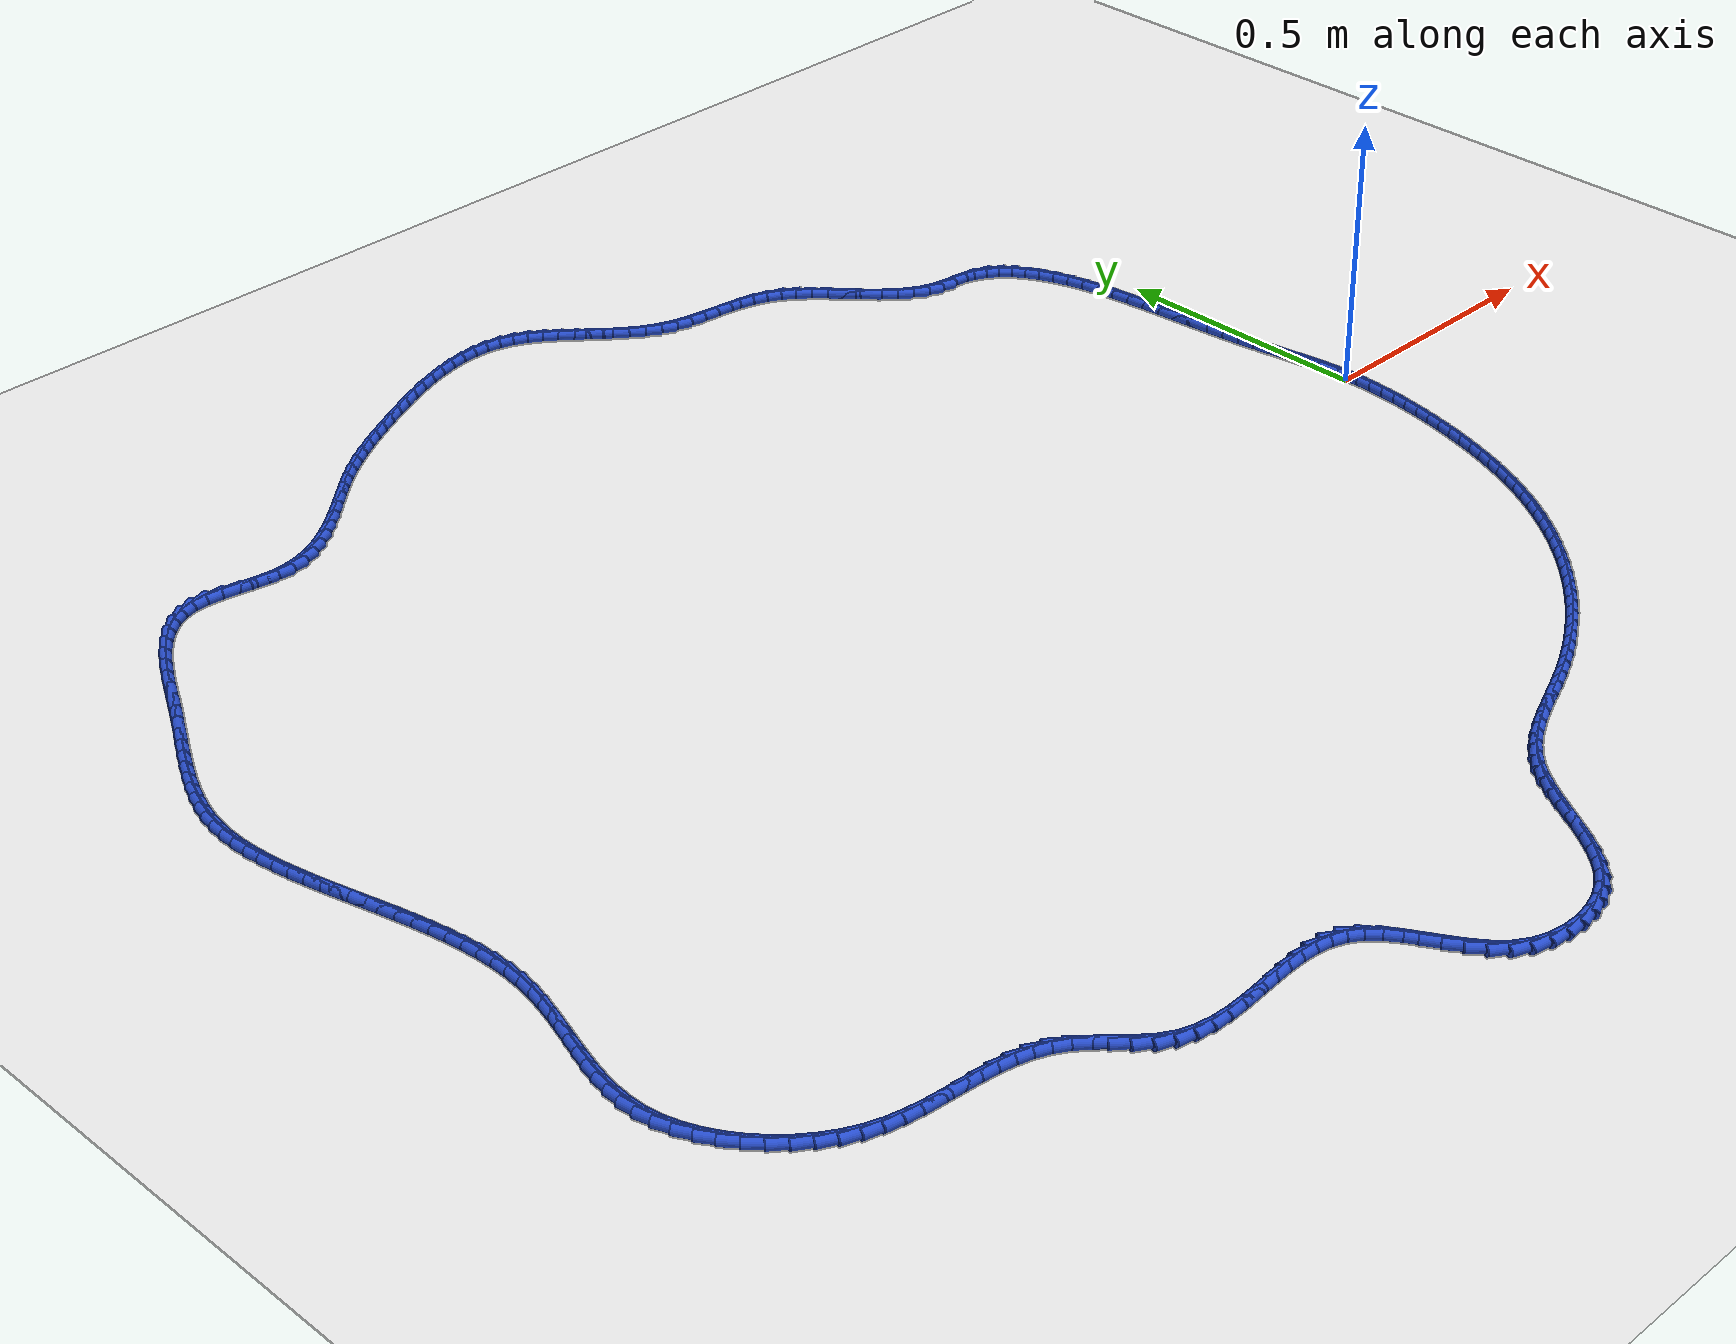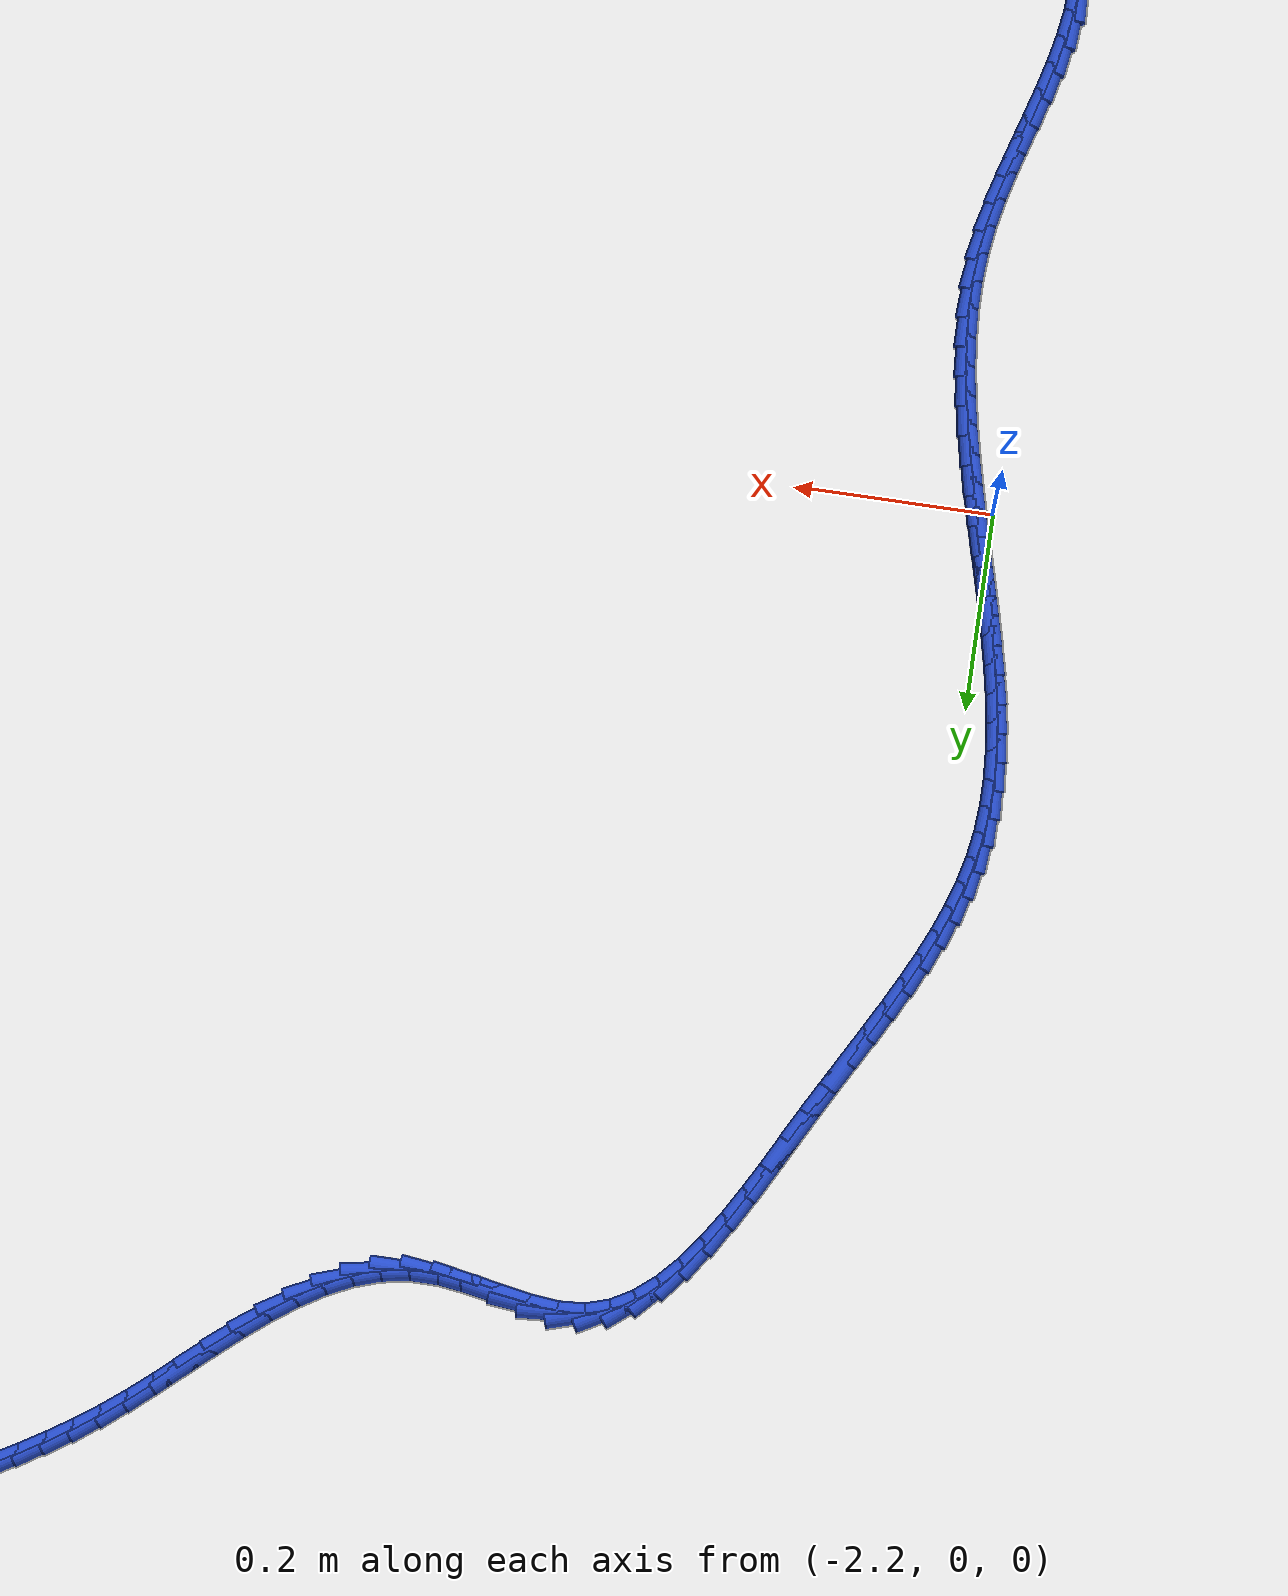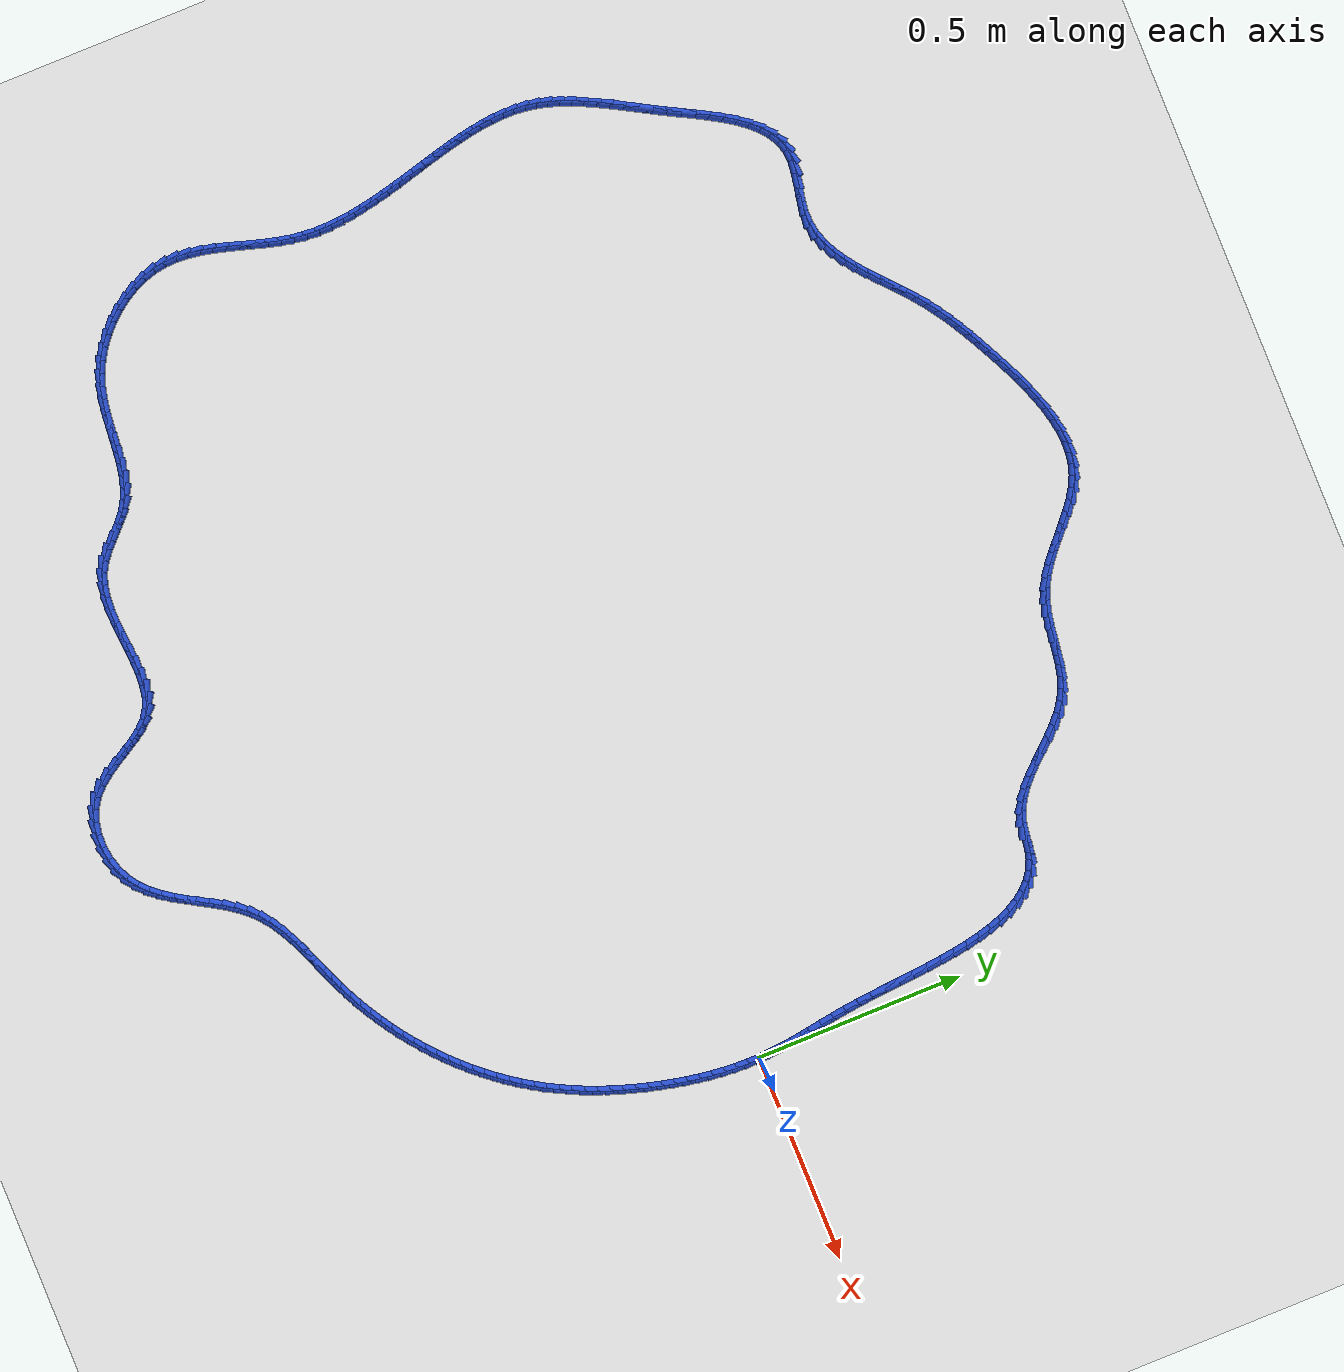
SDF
<sdf version="1.6">
 <world name="default">
  <light name="sun" type="directional">
   <pose>0 0 10 0 -0 0</pose>
   <diffuse>0.8 0.8 0.8 1</diffuse>
   <specular>0.2 0.2 0.2 1</specular>
   <attenuation>
    <range>1000</range>
    <constant>0.9</constant>
    <linear>0.01</linear>
    <quadratic>0.001</quadratic>
   </attenuation>
   <direction>-0.5 0.1 -0.9</direction>
  </light>
  <model name="ground_plane">
   <static>1</static>
   <link name="link">
    <collision name="collision">
     <geometry><plane><normal>0 0 1</normal><size>100 100</size></plane></geometry>
     <surface><friction><ode><mu>100</mu><mu2>50</mu2></ode></friction></surface>
    </collision>
    <visual name="visual">
     <cast_shadows>0</cast_shadows>
     <geometry><plane><normal>0 0 1</normal><size>100 100</size></plane></geometry>
     <material>
      <script><uri>file://media/materials/scripts/gazebo.material</uri><name>Gazebo/WhiteGlow</name></script>
     </material>
    </visual>
   </link>
  </model>
  <gravity>0 0 -9.8</gravity>
  <magnetic_field>6e-06 2.3e-05 -4.2e-05</magnetic_field>
  <atmosphere type="adiabatic"/>
  <physics name="default_physics" default="0" type="ode">
   <max_step_size>0.001</max_step_size>
   <real_time_factor>1</real_time_factor>
   <real_time_update_rate>1000</real_time_update_rate>
  </physics>
  <scene><ambient>0.4 0.4 0.4 1</ambient><background>0.7 0.7 0.7 1</background><shadows>1</shadows></scene>
  <spherical_coordinates>
   <surface_model>EARTH_WGS84</surface_model>
   <latitude_deg>0</latitude_deg>
   <longitude_deg>0</longitude_deg>
   <elevation>0</elevation>
   <heading_deg>0</heading_deg>
  </spherical_coordinates>
  <model name="line">
   <link name="link_0">
    <pose>-5.204170427930421e-18 9.71445146547012e-17 0.01 0 1.57 -1.516858598603744</pose>
    <collision name="collision">
     <geometry><cylinder><radius>0.01</radius><length>0.08</length></cylinder></geometry>
    </collision>
    <visual name="visual">
     <material>
      <script><name>Gazebo/Blue</name><uri>file://media/materials/scripts/gazebo.material</uri></script>
     </material>
     <geometry><cylinder><radius>0.01</radius><length>0.08</length></cylinder></geometry>
    </visual>
   </link>
   <link name="link_1">
    <pose>-0.0015242391956589154 0.028231829824980622 0.01 0 1.57 -1.4789966597970252</pose>
    <collision name="collision">
     <geometry><cylinder><radius>0.01</radius><length>0.08</length></cylinder></geometry>
    </collision>
    <visual name="visual">
     <material>
      <script><name>Gazebo/Blue</name><uri>file://media/materials/scripts/gazebo.material</uri></script>
     </material>
     <geometry><cylinder><radius>0.01</radius><length>0.08</length></cylinder></geometry>
    </visual>
   </link>
   <link name="link_2">
    <pose>-0.00410380521407094 0.05625280063618436 0.01 0 1.57 -1.449569584046951</pose>
    <collision name="collision">
     <geometry><cylinder><radius>0.01</radius><length>0.08</length></cylinder></geometry>
    </collision>
    <visual name="visual">
     <material>
      <script><name>Gazebo/Blue</name><uri>file://media/materials/scripts/gazebo.material</uri></script>
     </material>
     <geometry><cylinder><radius>0.01</radius><length>0.08</length></cylinder></geometry>
    </visual>
   </link>
   <link name="link_3">
    <pose>-0.007517797307046079 0.08427674721994391 0.01 0 1.57 -1.4291379045538755</pose>
    <collision name="collision">
     <geometry><cylinder><radius>0.01</radius><length>0.08</length></cylinder></geometry>
    </collision>
    <visual name="visual">
     <material>
      <script><name>Gazebo/Blue</name><uri>file://media/materials/scripts/gazebo.material</uri></script>
     </material>
     <geometry><cylinder><radius>0.01</radius><length>0.08</length></cylinder></geometry>
    </visual>
   </link>
   <link name="link_4">
    <pose>-0.011545314726394319 0.1125175043625919 0.01 0 1.57 -1.4178350203846481</pose>
    <collision name="collision">
     <geometry><cylinder><radius>0.01</radius><length>0.08</length></cylinder></geometry>
    </collision>
    <visual name="visual">
     <material>
      <script><name>Gazebo/Blue</name><uri>file://media/materials/scripts/gazebo.material</uri></script>
     </material>
     <geometry><cylinder><radius>0.01</radius><length>0.08</length></cylinder></geometry>
    </visual>
   </link>
   <link name="link_5">
    <pose>-0.01596545672392564 0.14118890685046093 0.01 0 1.57 -1.4154246961774581</pose>
    <collision name="collision">
     <geometry><cylinder><radius>0.01</radius><length>0.08</length></cylinder></geometry>
    </collision>
    <visual name="visual">
     <material>
      <script><name>Gazebo/Blue</name><uri>file://media/materials/scripts/gazebo.material</uri></script>
     </material>
     <geometry><cylinder><radius>0.01</radius><length>0.08</length></cylinder></geometry>
    </visual>
   </link>
   <link name="link_6">
    <pose>-0.02055732255145006 0.17050478946988357 0.01 0 1.57 -1.4213697091263997</pose>
    <collision name="collision">
     <geometry><cylinder><radius>0.01</radius><length>0.08</length></cylinder></geometry>
    </collision>
    <visual name="visual">
     <material>
      <script><name>Gazebo/Blue</name><uri>file://media/materials/scripts/gazebo.material</uri></script>
     </material>
     <geometry><cylinder><radius>0.01</radius><length>0.08</length></cylinder></geometry>
    </visual>
   </link>
   <link name="link_7">
    <pose>-0.02510001146077753 0.20067898700719247 0.01 0 1.57 -1.4348995871312127</pose>
    <collision name="collision">
     <geometry><cylinder><radius>0.01</radius><length>0.08</length></cylinder></geometry>
    </collision>
    <visual name="visual">
     <material>
      <script><name>Gazebo/Blue</name><uri>file://media/materials/scripts/gazebo.material</uri></script>
     </material>
     <geometry><cylinder><radius>0.01</radius><length>0.08</length></cylinder></geometry>
    </visual>
   </link>
   <link name="link_8">
    <pose>-0.02937262270371808 0.2319253342487203 0.01 0 1.57 -1.4548000202109357</pose>
    <collision name="collision">
     <geometry><cylinder><radius>0.01</radius><length>0.08</length></cylinder></geometry>
    </collision>
    <visual name="visual">
     <material>
      <script><name>Gazebo/Blue</name><uri>file://media/materials/scripts/gazebo.material</uri></script>
     </material>
     <geometry><cylinder><radius>0.01</radius><length>0.08</length></cylinder></geometry>
    </visual>
   </link>
   <link name="link_9">
    <pose>-0.03316213859478871 0.2644479599883298 0.01 0 1.57 -1.4735349088852516</pose>
    <collision name="collision">
     <geometry><cylinder><radius>0.01</radius><length>0.08</length></cylinder></geometry>
    </collision>
    <visual name="visual">
     <material>
      <script><name>Gazebo/Blue</name><uri>file://media/materials/scripts/gazebo.material</uri></script>
     </material>
     <geometry><cylinder><radius>0.01</radius><length>0.08</length></cylinder></geometry>
    </visual>
   </link>
   <link name="link_10">
    <pose>-0.036455739651285894 0.29820449970620355 0.01 0 1.57 -1.4846355746560118</pose>
    <collision name="collision">
     <geometry><cylinder><radius>0.01</radius><length>0.08</length></cylinder></geometry>
    </collision>
    <visual name="visual">
     <material>
      <script><name>Gazebo/Blue</name><uri>file://media/materials/scripts/gazebo.material</uri></script>
     </material>
     <geometry><cylinder><radius>0.01</radius><length>0.08</length></cylinder></geometry>
    </visual>
   </link>
   <link name="link_11">
    <pose>-0.03945189641128605 0.332892438808014 0.01 0 1.57 -1.4886325579227337</pose>
    <collision name="collision">
     <geometry><cylinder><radius>0.01</radius><length>0.08</length></cylinder></geometry>
    </collision>
    <visual name="visual">
     <material>
      <script><name>Gazebo/Blue</name><uri>file://media/materials/scripts/gazebo.material</uri></script>
     </material>
     <geometry><cylinder><radius>0.01</radius><length>0.08</length></cylinder></geometry>
    </visual>
   </link>
   <link name="link_12">
    <pose>-0.04235918286147937 0.36819682286484146 0.01 0 1.57 -1.4859864672699152</pose>
    <collision name="collision">
     <geometry><cylinder><radius>0.01</radius><length>0.08</length></cylinder></geometry>
    </collision>
    <visual name="visual">
     <material>
      <script><name>Gazebo/Blue</name><uri>file://media/materials/scripts/gazebo.material</uri></script>
     </material>
     <geometry><cylinder><radius>0.01</radius><length>0.08</length></cylinder></geometry>
    </visual>
   </link>
   <link name="link_13">
    <pose>-0.045386172988555955 0.4038026974477652 0.01 0 1.57 -1.4768049021204428</pose>
    <collision name="collision">
     <geometry><cylinder><radius>0.01</radius><length>0.08</length></cylinder></geometry>
    </collision>
    <visual name="visual">
     <material>
      <script><name>Gazebo/Blue</name><uri>file://media/materials/scripts/gazebo.material</uri></script>
     </material>
     <geometry><cylinder><radius>0.01</radius><length>0.08</length></cylinder></geometry>
    </visual>
   </link>
   <link name="link_14">
    <pose>-0.048741440779205975 0.4393951081278654 0.01 0 1.57 -1.4608703247317854</pose>
    <collision name="collision">
     <geometry><cylinder><radius>0.01</radius><length>0.08</length></cylinder></geometry>
    </collision>
    <visual name="visual">
     <material>
      <script><name>Gazebo/Blue</name><uri>file://media/materials/scripts/gazebo.material</uri></script>
     </material>
     <geometry><cylinder><radius>0.01</radius><length>0.08</length></cylinder></geometry>
    </visual>
   </link>
   <link name="link_15">
    <pose>-0.05263356022011952 0.47465910047622173 0.01 0 1.57 -1.4376357395155566</pose>
    <collision name="collision">
     <geometry><cylinder><radius>0.01</radius><length>0.08</length></cylinder></geometry>
    </collision>
    <visual name="visual">
     <material>
      <script><name>Gazebo/Blue</name><uri>file://media/materials/scripts/gazebo.material</uri></script>
     </material>
     <geometry><cylinder><radius>0.01</radius><length>0.08</length></cylinder></geometry>
    </visual>
   </link>
   <link name="link_16">
    <pose>-0.05727110529798679 0.5092797200639141 0.01 0 1.57 -1.406192172854888</pose>
    <collision name="collision">
     <geometry><cylinder><radius>0.01</radius><length>0.08</length></cylinder></geometry>
    </collision>
    <visual name="visual">
     <material>
      <script><name>Gazebo/Blue</name><uri>file://media/materials/scripts/gazebo.material</uri></script>
     </material>
     <geometry><cylinder><radius>0.01</radius><length>0.08</length></cylinder></geometry>
    </visual>
   </link>
   <link name="link_17">
    <pose>-0.0628626499994979 0.5429420124620222 0.01 0 1.57 -1.3652113379434214</pose>
    <collision name="collision">
     <geometry><cylinder><radius>0.01</radius><length>0.08</length></cylinder></geometry>
    </collision>
    <visual name="visual">
     <material>
      <script><name>Gazebo/Blue</name><uri>file://media/materials/scripts/gazebo.material</uri></script>
     </material>
     <geometry><cylinder><radius>0.01</radius><length>0.08</length></cylinder></geometry>
    </visual>
   </link>
   <link name="link_18">
    <pose>-0.06961676831134296 0.575331023241626 0.01 0 1.57 -1.3128715349806683</pose>
    <collision name="collision">
     <geometry><cylinder><radius>0.01</radius><length>0.08</length></cylinder></geometry>
    </collision>
    <visual name="visual">
     <material>
      <script><name>Gazebo/Blue</name><uri>file://media/materials/scripts/gazebo.material</uri></script>
     </material>
     <geometry><cylinder><radius>0.01</radius><length>0.08</length></cylinder></geometry>
    </visual>
   </link>
   <link name="link_19">
    <pose>-0.07774203422021211 0.6061317979738052 0.01 0 1.57 -1.2467907625518801</pose>
    <collision name="collision">
     <geometry><cylinder><radius>0.01</radius><length>0.08</length></cylinder></geometry>
    </collision>
    <visual name="visual">
     <material>
      <script><name>Gazebo/Blue</name><uri>file://media/materials/scripts/gazebo.material</uri></script>
     </material>
     <geometry><cylinder><radius>0.01</radius><length>0.08</length></cylinder></geometry>
    </visual>
   </link>
   <link name="link_20">
    <pose>-0.08744702171279554 0.6350293822296396 0.01 0 1.57 -1.164030238656246</pose>
    <collision name="collision">
     <geometry><cylinder><radius>0.01</radius><length>0.08</length></cylinder></geometry>
    </collision>
    <visual name="visual">
     <material>
      <script><name>Gazebo/Blue</name><uri>file://media/materials/scripts/gazebo.material</uri></script>
     </material>
     <geometry><cylinder><radius>0.01</radius><length>0.08</length></cylinder></geometry>
    </visual>
   </link>
   <link name="link_21">
    <pose>-0.09894030477578336 0.6617088215802092 0.01 0 1.57 -1.0613110632510085</pose>
    <collision name="collision">
     <geometry><cylinder><radius>0.01</radius><length>0.08</length></cylinder></geometry>
    </collision>
    <visual name="visual">
     <material>
      <script><name>Gazebo/Blue</name><uri>file://media/materials/scripts/gazebo.material</uri></script>
     </material>
     <geometry><cylinder><radius>0.01</radius><length>0.08</length></cylinder></geometry>
    </visual>
   </link>
   <link name="link_22">
    <pose>-0.11243045739586567 0.6858551615965937 0.01 0 1.57 -0.9357050187044735</pose>
    <collision name="collision">
     <geometry><cylinder><radius>0.01</radius><length>0.08</length></cylinder></geometry>
    </collision>
    <visual name="visual">
     <material>
      <script><name>Gazebo/Blue</name><uri>file://media/materials/scripts/gazebo.material</uri></script>
     </material>
     <geometry><cylinder><radius>0.01</radius><length>0.08</length></cylinder></geometry>
    </visual>
   </link>
   <link name="link_23">
    <pose>-0.1281260535597327 0.7071534478498729 0.01 0 1.57 -0.7861062455955061</pose>
    <collision name="collision">
     <geometry><cylinder><radius>0.01</radius><length>0.08</length></cylinder></geometry>
    </collision>
    <visual name="visual">
     <material>
      <script><name>Gazebo/Blue</name><uri>file://media/materials/scripts/gazebo.material</uri></script>
     </material>
     <geometry><cylinder><radius>0.01</radius><length>0.08</length></cylinder></geometry>
    </visual>
   </link>
   <link name="link_24">
    <pose>-0.14623566725407453 0.7252887259111266 0.01 0 1.57 -0.615397144577165</pose>
    <collision name="collision">
     <geometry><cylinder><radius>0.01</radius><length>0.08</length></cylinder></geometry>
    </collision>
    <visual name="visual">
     <material>
      <script><name>Gazebo/Blue</name><uri>file://media/materials/scripts/gazebo.material</uri></script>
     </material>
     <geometry><cylinder><radius>0.01</radius><length>0.08</length></cylinder></geometry>
    </visual>
   </link>
   <link name="link_25">
    <pose>-0.16696787246558129 0.7399460413514347 0.01 0 1.57 -0.43202273848234357</pose>
    <collision name="collision">
     <geometry><cylinder><radius>0.01</radius><length>0.08</length></cylinder></geometry>
    </collision>
    <visual name="visual">
     <material>
      <script><name>Gazebo/Blue</name><uri>file://media/materials/scripts/gazebo.material</uri></script>
     </material>
     <geometry><cylinder><radius>0.01</radius><length>0.08</length></cylinder></geometry>
    </visual>
   </link>
   <link name="link_26">
    <pose>-0.1905312431809431 0.7508104397418768 0.01 0 1.57 -0.24878445954260098</pose>
    <collision name="collision">
     <geometry><cylinder><radius>0.01</radius><length>0.08</length></cylinder></geometry>
    </collision>
    <visual name="visual">
     <material>
      <script><name>Gazebo/Blue</name><uri>file://media/materials/scripts/gazebo.material</uri></script>
     </material>
     <geometry><cylinder><radius>0.01</radius><length>0.08</length></cylinder></geometry>
    </visual>
   </link>
   <link name="link_27">
    <pose>-0.21713336743947712 0.7575686436825962 0.01 0 1.57 -0.12048639819023885</pose>
    <collision name="collision">
     <geometry><cylinder><radius>0.01</radius><length>0.08</length></cylinder></geometry>
    </collision>
    <visual name="visual">
     <material>
      <script><name>Gazebo/Blue</name><uri>file://media/materials/scripts/gazebo.material</uri></script>
     </material>
     <geometry><cylinder><radius>0.01</radius><length>0.08</length></cylinder></geometry>
    </visual>
   </link>
   <link name="link_28">
    <pose>-0.24628199617381558 0.761097750838022 0.01 0 1.57 -0.15106599381150962</pose>
    <collision name="collision">
     <geometry><cylinder><radius>0.01</radius><length>0.08</length></cylinder></geometry>
    </collision>
    <visual name="visual">
     <material>
      <script><name>Gazebo/Blue</name><uri>file://media/materials/scripts/gazebo.material</uri></script>
     </material>
     <geometry><cylinder><radius>0.01</radius><length>0.08</length></cylinder></geometry>
    </visual>
   </link>
   <link name="link_29">
    <pose>-0.2755569414976121 0.7655541509729111 0.01 0 1.57 -0.3246735706186334</pose>
    <collision name="collision">
     <geometry><cylinder><radius>0.01</radius><length>0.08</length></cylinder></geometry>
    </collision>
    <visual name="visual">
     <material>
      <script><name>Gazebo/Blue</name><uri>file://media/materials/scripts/gazebo.material</uri></script>
     </material>
     <geometry><cylinder><radius>0.01</radius><length>0.08</length></cylinder></geometry>
    </visual>
   </link>
   <link name="link_30">
    <pose>-0.3027434968607715 0.7747047188407985 0.01 0 1.57 -0.5051651830811787</pose>
    <collision name="collision">
     <geometry><cylinder><radius>0.01</radius><length>0.08</length></cylinder></geometry>
    </collision>
    <visual name="visual">
     <material>
      <script><name>Gazebo/Blue</name><uri>file://media/materials/scripts/gazebo.material</uri></script>
     </material>
     <geometry><cylinder><radius>0.01</radius><length>0.08</length></cylinder></geometry>
    </visual>
   </link>
   <link name="link_31">
    <pose>-0.32775527687636746 0.7885369395594293 0.01 0 1.57 -0.6462684504973066</pose>
    <collision name="collision">
     <geometry><cylinder><radius>0.01</radius><length>0.08</length></cylinder></geometry>
    </collision>
    <visual name="visual">
     <material>
      <script><name>Gazebo/Blue</name><uri>file://media/materials/scripts/gazebo.material</uri></script>
     </material>
     <geometry><cylinder><radius>0.01</radius><length>0.08</length></cylinder></geometry>
    </visual>
   </link>
   <link name="link_32">
    <pose>-0.3510354481746681 0.8060979404471559 0.01 0 1.57 -0.7463234699106328</pose>
    <collision name="collision">
     <geometry><cylinder><radius>0.01</radius><length>0.08</length></cylinder></geometry>
    </collision>
    <visual name="visual">
     <material>
      <script><name>Gazebo/Blue</name><uri>file://media/materials/scripts/gazebo.material</uri></script>
     </material>
     <geometry><cylinder><radius>0.01</radius><length>0.08</length></cylinder></geometry>
    </visual>
   </link>
   <link name="link_33">
    <pose>-0.37302717738594127 0.8264348488223299 0.01 0 1.57 -0.8087966572259719</pose>
    <collision name="collision">
     <geometry><cylinder><radius>0.01</radius><length>0.08</length></cylinder></geometry>
    </collision>
    <visual name="visual">
     <material>
      <script><name>Gazebo/Blue</name><uri>file://media/materials/scripts/gazebo.material</uri></script>
     </material>
     <geometry><cylinder><radius>0.01</radius><length>0.08</length></cylinder></geometry>
    </visual>
   </link>
   <link name="link_34">
    <pose>-0.3941736311404553 0.8485947920033033 0.01 0 1.57 -0.8375675524444928</pose>
    <collision name="collision">
     <geometry><cylinder><radius>0.01</radius><length>0.08</length></cylinder></geometry>
    </collision>
    <visual name="visual">
     <material>
      <script><name>Gazebo/Blue</name><uri>file://media/materials/scripts/gazebo.material</uri></script>
     </material>
     <geometry><cylinder><radius>0.01</radius><length>0.08</length></cylinder></geometry>
    </visual>
   </link>
   <link name="link_35">
    <pose>-0.4149179760684781 0.8716248973084288 0.01 0 1.57 -0.8347943476413795</pose>
    <collision name="collision">
     <geometry><cylinder><radius>0.01</radius><length>0.08</length></cylinder></geometry>
    </collision>
    <visual name="visual">
     <material>
      <script><name>Gazebo/Blue</name><uri>file://media/materials/scripts/gazebo.material</uri></script>
     </material>
     <geometry><cylinder><radius>0.01</radius><length>0.08</length></cylinder></geometry>
    </visual>
   </link>
   <link name="link_36">
    <pose>-0.4357033788002779 0.8945722920560584 0.01 0 1.57 -0.8002688352596079</pose>
    <collision name="collision">
     <geometry><cylinder><radius>0.01</radius><length>0.08</length></cylinder></geometry>
    </collision>
    <visual name="visual">
     <material>
      <script><name>Gazebo/Blue</name><uri>file://media/materials/scripts/gazebo.material</uri></script>
     </material>
     <geometry><cylinder><radius>0.01</radius><length>0.08</length></cylinder></geometry>
    </visual>
   </link>
   <link name="link_37">
    <pose>-0.4569730059661225 0.9164841035645438 0.01 0 1.57 -0.731470386488567</pose>
    <collision name="collision">
     <geometry><cylinder><radius>0.01</radius><length>0.08</length></cylinder></geometry>
    </collision>
    <visual name="visual">
     <material>
      <script><name>Gazebo/Blue</name><uri>file://media/materials/scripts/gazebo.material</uri></script>
     </material>
     <geometry><cylinder><radius>0.01</radius><length>0.08</length></cylinder></geometry>
    </visual>
   </link>
   <link name="link_38">
    <pose>-0.4791700241962805 0.9364074591522377 0.01 0 1.57 -0.6243966374171955</pose>
    <collision name="collision">
     <geometry><cylinder><radius>0.01</radius><length>0.08</length></cylinder></geometry>
    </collision>
    <visual name="visual">
     <material>
      <script><name>Gazebo/Blue</name><uri>file://media/materials/scripts/gazebo.material</uri></script>
     </material>
     <geometry><cylinder><radius>0.01</radius><length>0.08</length></cylinder></geometry>
    </visual>
   </link>
   <link name="link_39">
    <pose>-0.5027376001210196 0.9533894861374914 0.01 0 1.57 -0.4777440140927641</pose>
    <collision name="collision">
     <geometry><cylinder><radius>0.01</radius><length>0.08</length></cylinder></geometry>
    </collision>
    <visual name="visual">
     <material>
      <script><name>Gazebo/Blue</name><uri>file://media/materials/scripts/gazebo.material</uri></script>
     </material>
     <geometry><cylinder><radius>0.01</radius><length>0.08</length></cylinder></geometry>
    </visual>
   </link>
   <link name="link_40">
    <pose>-0.528099369246484 0.9665204600480207 0.01 0 1.57 -0.3308523900748825</pose>
    <collision name="collision">
     <geometry><cylinder><radius>0.01</radius><length>0.08</length></cylinder></geometry>
    </collision>
    <visual name="visual">
     <material>
      <script><name>Gazebo/Blue</name><uri>file://media/materials/scripts/gazebo.material</uri></script>
     </material>
     <geometry><cylinder><radius>0.01</radius><length>0.08</length></cylinder></geometry>
    </visual>
   </link>
   <link name="link_41">
    <pose>-0.5552469599160308 0.9758450477403315 0.01 0 1.57 -0.2241033917324248</pose>
    <collision name="collision">
     <geometry><cylinder><radius>0.01</radius><length>0.08</length></cylinder></geometry>
    </collision>
    <visual name="visual">
     <material>
      <script><name>Gazebo/Blue</name><uri>file://media/materials/scripts/gazebo.material</uri></script>
     </material>
     <geometry><cylinder><radius>0.01</radius><length>0.08</length></cylinder></geometry>
    </visual>
   </link>
   <link name="link_42">
    <pose>-0.583749342786046 0.9823416525138474 0.01 0 1.57 -0.15801478090528873</pose>
    <collision name="collision">
     <geometry><cylinder><radius>0.01</radius><length>0.08</length></cylinder></geometry>
    </collision>
    <visual name="visual">
     <material>
      <script><name>Gazebo/Blue</name><uri>file://media/materials/scripts/gazebo.material</uri></script>
     </material>
     <geometry><cylinder><radius>0.01</radius><length>0.08</length></cylinder></geometry>
    </visual>
   </link>
   <link name="link_43">
    <pose>-0.6131578275645698 0.9870276942802381 0.01 0 1.57 -0.1296151906768664</pose>
    <collision name="collision">
     <geometry><cylinder><radius>0.01</radius><length>0.08</length></cylinder></geometry>
    </collision>
    <visual name="visual">
     <material>
      <script><name>Gazebo/Blue</name><uri>file://media/materials/scripts/gazebo.material</uri></script>
     </material>
     <geometry><cylinder><radius>0.01</radius><length>0.08</length></cylinder></geometry>
    </visual>
   </link>
   <link name="link_44">
    <pose>-0.6430237239596437 0.9909205929511744 0.01 0 1.57 -0.13695247013905812</pose>
    <collision name="collision">
     <geometry><cylinder><radius>0.01</radius><length>0.08</length></cylinder></geometry>
    </collision>
    <visual name="visual">
     <material>
      <script><name>Gazebo/Blue</name><uri>file://media/materials/scripts/gazebo.material</uri></script>
     </material>
     <geometry><cylinder><radius>0.01</radius><length>0.08</length></cylinder></geometry>
    </visual>
   </link>
   <link name="link_45">
    <pose>-0.6728983416793081 0.995037768438326 0.01 0 1.57 -0.18008757190425403</pose>
    <collision name="collision">
     <geometry><cylinder><radius>0.01</radius><length>0.08</length></cylinder></geometry>
    </collision>
    <visual name="visual">
     <material>
      <script><name>Gazebo/Blue</name><uri>file://media/materials/scripts/gazebo.material</uri></script>
     </material>
     <geometry><cylinder><radius>0.01</radius><length>0.08</length></cylinder></geometry>
    </visual>
   </link>
   <link name="link_46">
    <pose>-0.7023329904316039 1.0003966406533638 0.01 0 1.57 -0.26078962087005764</pose>
    <collision name="collision">
     <geometry><cylinder><radius>0.01</radius><length>0.08</length></cylinder></geometry>
    </collision>
    <visual name="visual">
     <material>
      <script><name>Gazebo/Blue</name><uri>file://media/materials/scripts/gazebo.material</uri></script>
     </material>
     <geometry><cylinder><radius>0.01</radius><length>0.08</length></cylinder></geometry>
    </visual>
   </link>
   <link name="link_47">
    <pose>-0.7308789799245717 1.0080146295079573 0.01 0 1.57 -0.38032868947462684</pose>
    <collision name="collision">
     <geometry><cylinder><radius>0.01</radius><length>0.08</length></cylinder></geometry>
    </collision>
    <visual name="visual">
     <material>
      <script><name>Gazebo/Blue</name><uri>file://media/materials/scripts/gazebo.material</uri></script>
     </material>
     <geometry><cylinder><radius>0.01</radius><length>0.08</length></cylinder></geometry>
    </visual>
   </link>
   <link name="link_48">
    <pose>-0.7580934111212514 1.018894793010358 0.01 0 1.57 -0.5106499918133155</pose>
    <collision name="collision">
     <geometry><cylinder><radius>0.01</radius><length>0.08</length></cylinder></geometry>
    </collision>
    <visual name="visual">
     <material>
      <script><name>Gazebo/Blue</name><uri>file://media/materials/scripts/gazebo.material</uri></script>
     </material>
     <geometry><cylinder><radius>0.01</radius><length>0.08</length></cylinder></geometry>
    </visual>
   </link>
   <link name="link_49">
    <pose>-0.7838273211551451 1.0333112482237796 0.01 0 1.57 -0.6105952761726736</pose>
    <collision name="collision">
     <geometry><cylinder><radius>0.01</radius><length>0.08</length></cylinder></geometry>
    </collision>
    <visual name="visual">
     <material>
      <script><name>Gazebo/Blue</name><uri>file://media/materials/scripts/gazebo.material</uri></script>
     </material>
     <geometry><cylinder><radius>0.01</radius><length>0.08</length></cylinder></geometry>
    </visual>
   </link>
   <link name="link_50">
    <pose>-0.8083589712020148 1.0504786267571098 0.01 0 1.57 -0.6782524625308244</pose>
    <collision name="collision">
     <geometry><cylinder><radius>0.01</radius><length>0.08</length></cylinder></geometry>
    </collision>
    <visual name="visual">
     <material>
      <script><name>Gazebo/Blue</name><uri>file://media/materials/scripts/gazebo.material</uri></script>
     </material>
     <geometry><cylinder><radius>0.01</radius><length>0.08</length></cylinder></geometry>
    </visual>
   </link>
   <link name="link_51">
    <pose>-0.8320002453536192 1.0695281777620058 0.01 0 1.57 -0.7159504403387272</pose>
    <collision name="collision">
     <geometry><cylinder><radius>0.01</radius><length>0.08</length></cylinder></geometry>
    </collision>
    <visual name="visual">
     <material>
      <script><name>Gazebo/Blue</name><uri>file://media/materials/scripts/gazebo.material</uri></script>
     </material>
     <geometry><cylinder><radius>0.01</radius><length>0.08</length></cylinder></geometry>
    </visual>
   </link>
   <link name="link_52">
    <pose>-0.8550630277017169 1.0895911503901243 0.01 0 1.57 -0.7252776468707932</pose>
    <collision name="collision">
     <geometry><cylinder><radius>0.01</radius><length>0.08</length></cylinder></geometry>
    </collision>
    <visual name="visual">
     <material>
      <script><name>Gazebo/Blue</name><uri>file://media/materials/scripts/gazebo.material</uri></script>
     </material>
     <geometry><cylinder><radius>0.01</radius><length>0.08</length></cylinder></geometry>
    </visual>
   </link>
   <link name="link_53">
    <pose>-0.877859202338067 1.109798793793123 0.01 0 1.57 -0.7062282164427797</pose>
    <collision name="collision">
     <geometry><cylinder><radius>0.01</radius><length>0.08</length></cylinder></geometry>
    </collision>
    <visual name="visual">
     <material>
      <script><name>Gazebo/Blue</name><uri>file://media/materials/scripts/gazebo.material</uri></script>
     </material>
     <geometry><cylinder><radius>0.01</radius><length>0.08</length></cylinder></geometry>
    </visual>
   </link>
   <link name="link_54">
    <pose>-0.9007006533544285 1.1292823571226596 0.01 0 1.57 -0.6569306301226311</pose>
    <collision name="collision">
     <geometry><cylinder><radius>0.01</radius><length>0.08</length></cylinder></geometry>
    </collision>
    <visual name="visual">
     <material>
      <script><name>Gazebo/Blue</name><uri>file://media/materials/scripts/gazebo.material</uri></script>
     </material>
     <geometry><cylinder><radius>0.01</radius><length>0.08</length></cylinder></geometry>
    </visual>
   </link>
   <link name="link_55">
    <pose>-0.9238992648425601 1.1471730895303913 0.01 0 1.57 -0.5738727392508818</pose>
    <collision name="collision">
     <geometry><cylinder><radius>0.01</radius><length>0.08</length></cylinder></geometry>
    </collision>
    <visual name="visual">
     <material>
      <script><name>Gazebo/Blue</name><uri>file://media/materials/scripts/gazebo.material</uri></script>
     </material>
     <geometry><cylinder><radius>0.01</radius><length>0.08</length></cylinder></geometry>
    </visual>
   </link>
   <link name="link_56">
    <pose>-0.9477669208942208 1.1626022401679745 0.01 0 1.57 -0.4531141646685122</pose>
    <collision name="collision">
     <geometry><cylinder><radius>0.01</radius><length>0.08</length></cylinder></geometry>
    </collision>
    <visual name="visual">
     <material>
      <script><name>Gazebo/Blue</name><uri>file://media/materials/scripts/gazebo.material</uri></script>
     </material>
     <geometry><cylinder><radius>0.01</radius><length>0.08</length></cylinder></geometry>
    </visual>
   </link>
   <link name="link_57">
    <pose>-0.9726155056011692 1.1747010581870674 0.01 0 1.57 -0.30061159492986833</pose>
    <collision name="collision">
     <geometry><cylinder><radius>0.01</radius><length>0.08</length></cylinder></geometry>
    </collision>
    <visual name="visual">
     <material>
      <script><name>Gazebo/Blue</name><uri>file://media/materials/scripts/gazebo.material</uri></script>
     </material>
     <geometry><cylinder><radius>0.01</radius><length>0.08</length></cylinder></geometry>
    </visual>
   </link>
   <link name="link_58">
    <pose>-0.9986831664420575 1.1827822023384595 0.01 0 1.57 -0.15334032017988866</pose>
    <collision name="collision">
     <geometry><cylinder><radius>0.01</radius><length>0.08</length></cylinder></geometry>
    </collision>
    <visual name="visual">
     <material>
      <script><name>Gazebo/Blue</name><uri>file://media/materials/scripts/gazebo.material</uri></script>
     </material>
     <geometry><cylinder><radius>0.01</radius><length>0.08</length></cylinder></geometry>
    </visual>
   </link>
   <link name="link_59">
    <pose>-1.0258722916813732 1.1869843788665806 0.01 0 1.57 -0.024780535889872394</pose>
    <collision name="collision">
     <geometry><cylinder><radius>0.01</radius><length>0.08</length></cylinder></geometry>
    </collision>
    <visual name="visual">
     <material>
      <script><name>Gazebo/Blue</name><uri>file://media/materials/scripts/gazebo.material</uri></script>
     </material>
     <geometry><cylinder><radius>0.01</radius><length>0.08</length></cylinder></geometry>
    </visual>
   </link>
   <link name="link_60">
    <pose>-1.0539897530955762 1.1876812872854638 0.01 0 1.57 0.08418251228025432</pose>
    <collision name="collision">
     <geometry><cylinder><radius>0.01</radius><length>0.08</length></cylinder></geometry>
    </collision>
    <visual name="visual">
     <material>
      <script><name>Gazebo/Blue</name><uri>file://media/materials/scripts/gazebo.material</uri></script>
     </material>
     <geometry><cylinder><radius>0.01</radius><length>0.08</length></cylinder></geometry>
    </visual>
   </link>
   <link name="link_61">
    <pose>-1.0828424156970546 1.1852466437503728 0.01 0 1.57 0.1748429041281084</pose>
    <collision name="collision">
     <geometry><cylinder><radius>0.01</radius><length>0.08</length></cylinder></geometry>
    </collision>
    <visual name="visual">
     <material>
      <script><name>Gazebo/Blue</name><uri>file://media/materials/scripts/gazebo.material</uri></script>
     </material>
     <geometry><cylinder><radius>0.01</radius><length>0.08</length></cylinder></geometry>
    </visual>
   </link>
   <link name="link_62">
    <pose>-1.1122371444981942 1.1800541644165696 0.01 0 1.57 0.24942533777935838</pose>
    <collision name="collision">
     <geometry><cylinder><radius>0.01</radius><length>0.08</length></cylinder></geometry>
    </collision>
    <visual name="visual">
     <material>
      <script><name>Gazebo/Blue</name><uri>file://media/materials/scripts/gazebo.material</uri></script>
     </material>
     <geometry><cylinder><radius>0.01</radius><length>0.08</length></cylinder></geometry>
    </visual>
   </link>
   <link name="link_63">
    <pose>-1.1419808045113828 1.172477565439318 0.01 0 1.57 0.31028462605610674</pose>
    <collision name="collision">
     <geometry><cylinder><radius>0.01</radius><length>0.08</length></cylinder></geometry>
    </collision>
    <visual name="visual">
     <material>
      <script><name>Gazebo/Blue</name><uri>file://media/materials/scripts/gazebo.material</uri></script>
     </material>
     <geometry><cylinder><radius>0.01</radius><length>0.08</length></cylinder></geometry>
    </visual>
   </link>
   <link name="link_64">
    <pose>-1.1718802607490075 1.16289056297388 0.01 0 1.57 0.3595160472740397</pose>
    <collision name="collision">
     <geometry><cylinder><radius>0.01</radius><length>0.08</length></cylinder></geometry>
    </collision>
    <visual name="visual">
     <material>
      <script><name>Gazebo/Blue</name><uri>file://media/materials/scripts/gazebo.material</uri></script>
     </material>
     <geometry><cylinder><radius>0.01</radius><length>0.08</length></cylinder></geometry>
    </visual>
   </link>
   <link name="link_65">
    <pose>-1.2017423782234538 1.151666873175518 0.01 0 1.57 0.3988142096564022</pose>
    <collision name="collision">
     <geometry><cylinder><radius>0.01</radius><length>0.08</length></cylinder></geometry>
    </collision>
    <visual name="visual">
     <material>
      <script><name>Gazebo/Blue</name><uri>file://media/materials/scripts/gazebo.material</uri></script>
     </material>
     <geometry><cylinder><radius>0.01</radius><length>0.08</length></cylinder></geometry>
    </visual>
   </link>
   <link name="link_66">
    <pose>-1.2313740219471103 1.1391802121994963 0.01 0 1.57 0.4294481745117285</pose>
    <collision name="collision">
     <geometry><cylinder><radius>0.01</radius><length>0.08</length></cylinder></geometry>
    </collision>
    <visual name="visual">
     <material>
      <script><name>Gazebo/Blue</name><uri>file://media/materials/scripts/gazebo.material</uri></script>
     </material>
     <geometry><cylinder><radius>0.01</radius><length>0.08</length></cylinder></geometry>
    </visual>
   </link>
   <link name="link_67">
    <pose>-1.2605820569323627 1.1258042962010761 0.01 0 1.57 0.45227430445376476</pose>
    <collision name="collision">
     <geometry><cylinder><radius>0.01</radius><length>0.08</length></cylinder></geometry>
    </collision>
    <visual name="visual">
     <material>
      <script><name>Gazebo/Blue</name><uri>file://media/materials/scripts/gazebo.material</uri></script>
     </material>
     <geometry><cylinder><radius>0.01</radius><length>0.08</length></cylinder></geometry>
    </visual>
   </link>
   <link name="link_68">
    <pose>-1.289173348191599 1.111912841335522 0.01 0 1.57 0.4677604209521697</pose>
    <collision name="collision">
     <geometry><cylinder><radius>0.01</radius><length>0.08</length></cylinder></geometry>
    </collision>
    <visual name="visual">
     <material>
      <script><name>Gazebo/Blue</name><uri>file://media/materials/scripts/gazebo.material</uri></script>
     </material>
     <geometry><cylinder><radius>0.01</radius><length>0.08</length></cylinder></geometry>
    </visual>
   </link>
   <link name="link_69">
    <pose>-1.3169551234946955 1.0978788320389177 0.01 0 1.57 0.47967126198886395</pose>
    <collision name="collision">
     <geometry><cylinder><radius>0.01</radius><length>0.08</length></cylinder></geometry>
    </collision>
    <visual name="visual">
     <material>
      <script><name>Gazebo/Blue</name><uri>file://media/materials/scripts/gazebo.material</uri></script>
     </material>
     <geometry><cylinder><radius>0.01</radius><length>0.08</length></cylinder></geometry>
    </visual>
   </link>
   <link name="link_70">
    <pose>-1.3438194016507499 1.0839042204982132 0.01 0 1.57 0.4964913899550093</pose>
    <collision name="collision">
     <geometry><cylinder><radius>0.01</radius><length>0.08</length></cylinder></geometry>
    </collision>
    <visual name="visual">
     <material>
      <script><name>Gazebo/Blue</name><uri>file://media/materials/scripts/gazebo.material</uri></script>
     </material>
     <geometry><cylinder><radius>0.01</radius><length>0.08</length></cylinder></geometry>
    </visual>
   </link>
   <link name="link_71">
    <pose>-1.3698514094422356 1.069801238541432 0.01 0 1.57 0.5194225142401093</pose>
    <collision name="collision">
     <geometry><cylinder><radius>0.01</radius><length>0.08</length></cylinder></geometry>
    </collision>
    <visual name="visual">
     <material>
      <script><name>Gazebo/Blue</name><uri>file://media/materials/scripts/gazebo.material</uri></script>
     </material>
     <geometry><cylinder><radius>0.01</radius><length>0.08</length></cylinder></geometry>
    </visual>
   </link>
   <link name="link_72">
    <pose>-1.3951631518309955 1.0553281036539617 0.01 0 1.57 0.548210332757114</pose>
    <collision name="collision">
     <geometry><cylinder><radius>0.01</radius><length>0.08</length></cylinder></geometry>
    </collision>
    <visual name="visual">
     <material>
      <script><name>Gazebo/Blue</name><uri>file://media/materials/scripts/gazebo.material</uri></script>
     </material>
     <geometry><cylinder><radius>0.01</radius><length>0.08</length></cylinder></geometry>
    </visual>
   </link>
   <link name="link_73">
    <pose>-1.419866633778871 1.04024303332119 0.01 0 1.57 0.5822792945771894</pose>
    <collision name="collision">
     <geometry><cylinder><radius>0.01</radius><length>0.08</length></cylinder></geometry>
    </collision>
    <visual name="visual">
     <material>
      <script><name>Gazebo/Blue</name><uri>file://media/materials/scripts/gazebo.material</uri></script>
     </material>
     <geometry><cylinder><radius>0.01</radius><length>0.08</length></cylinder></geometry>
    </visual>
   </link>
   <link name="link_74">
    <pose>-1.4440738602477041 1.0243042450285038 0.01 0 1.57 0.6207462131361181</pose>
    <collision name="collision">
     <geometry><cylinder><radius>0.01</radius><length>0.08</length></cylinder></geometry>
    </collision>
    <visual name="visual">
     <material>
      <script><name>Gazebo/Blue</name><uri>file://media/materials/scripts/gazebo.material</uri></script>
     </material>
     <geometry><cylinder><radius>0.01</radius><length>0.08</length></cylinder></geometry>
    </visual>
   </link>
   <link name="link_75">
    <pose>-1.467896836199337 1.0072699562612912 0.01 0 1.57 0.6624778548712713</pose>
    <collision name="collision">
     <geometry><cylinder><radius>0.01</radius><length>0.08</length></cylinder></geometry>
    </collision>
    <visual name="visual">
     <material>
      <script><name>Gazebo/Blue</name><uri>file://media/materials/scripts/gazebo.material</uri></script>
     </material>
     <geometry><cylinder><radius>0.01</radius><length>0.08</length></cylinder></geometry>
    </visual>
   </link>
   <link name="link_76">
    <pose>-1.4914475676875383 0.9888984325415573 0.01 0 1.57 0.7016660697950372</pose>
    <collision name="collision">
     <geometry><cylinder><radius>0.01</radius><length>0.08</length></cylinder></geometry>
    </collision>
    <visual name="visual">
     <material>
      <script><name>Gazebo/Blue</name><uri>file://media/materials/scripts/gazebo.material</uri></script>
     </material>
     <geometry><cylinder><radius>0.01</radius><length>0.08</length></cylinder></geometry>
    </visual>
   </link>
   <link name="link_77">
    <pose>-1.514842125236504 0.969126745694375 0.01 0 1.57 0.7237987166077713</pose>
    <collision name="collision">
     <geometry><cylinder><radius>0.01</radius><length>0.08</length></cylinder></geometry>
    </collision>
    <visual name="visual">
     <material>
      <script><name>Gazebo/Blue</name><uri>file://media/materials/scripts/gazebo.material</uri></script>
     </material>
     <geometry><cylinder><radius>0.01</radius><length>0.08</length></cylinder></geometry>
    </visual>
   </link>
   <link name="link_78">
    <pose>-1.538209812366686 0.9484741204183047 0.01 0 1.57 0.7273877888025314</pose>
    <collision name="collision">
     <geometry><cylinder><radius>0.01</radius><length>0.08</length></cylinder></geometry>
    </collision>
    <visual name="visual">
     <material>
      <script><name>Gazebo/Blue</name><uri>file://media/materials/scripts/gazebo.material</uri></script>
     </material>
     <geometry><cylinder><radius>0.01</radius><length>0.08</length></cylinder></geometry>
    </visual>
   </link>
   <link name="link_79">
    <pose>-1.5616826211500408 0.9275780575720696 0.01 0 1.57 0.7129672218733895</pose>
    <collision name="collision">
     <geometry><cylinder><radius>0.01</radius><length>0.08</length></cylinder></geometry>
    </collision>
    <visual name="visual">
     <material>
      <script><name>Gazebo/Blue</name><uri>file://media/materials/scripts/gazebo.material</uri></script>
     </material>
     <geometry><cylinder><radius>0.01</radius><length>0.08</length></cylinder></geometry>
    </visual>
   </link>
   <link name="link_80">
    <pose>-1.5853925436585254 0.9070760580143931 0.01 0 1.57 0.6799662331584919</pose>
    <collision name="collision">
     <geometry><cylinder><radius>0.01</radius><length>0.08</length></cylinder></geometry>
    </collision>
    <visual name="visual">
     <material>
      <script><name>Gazebo/Blue</name><uri>file://media/materials/scripts/gazebo.material</uri></script>
     </material>
     <geometry><cylinder><radius>0.01</radius><length>0.08</length></cylinder></geometry>
    </visual>
   </link>
   <link name="link_81">
    <pose>-1.609471571964096 0.8876056226039972 0.01 0 1.57 0.6267954406049271</pose>
    <collision name="collision">
     <geometry><cylinder><radius>0.01</radius><length>0.08</length></cylinder></geometry>
    </collision>
    <visual name="visual">
     <material>
      <script><name>Gazebo/Blue</name><uri>file://media/materials/scripts/gazebo.material</uri></script>
     </material>
     <geometry><cylinder><radius>0.01</radius><length>0.08</length></cylinder></geometry>
    </visual>
   </link>
   <link name="link_82">
    <pose>-1.6340516981387092 0.8698042521996056 0.01 0 1.57 0.5510500421278144</pose>
    <collision name="collision">
     <geometry><cylinder><radius>0.01</radius><length>0.08</length></cylinder></geometry>
    </collision>
    <visual name="visual">
     <material>
      <script><name>Gazebo/Blue</name><uri>file://media/materials/scripts/gazebo.material</uri></script>
     </material>
     <geometry><cylinder><radius>0.01</radius><length>0.08</length></cylinder></geometry>
    </visual>
   </link>
   <link name="link_83">
    <pose>-1.6592649142543223 0.8543094476599409 0.01 0 1.57 0.4500558443667388</pose>
    <collision name="collision">
     <geometry><cylinder><radius>0.01</radius><length>0.08</length></cylinder></geometry>
    </collision>
    <visual name="visual">
     <material>
      <script><name>Gazebo/Blue</name><uri>file://media/materials/scripts/gazebo.material</uri></script>
     </material>
     <geometry><cylinder><radius>0.01</radius><length>0.08</length></cylinder></geometry>
    </visual>
   </link>
   <link name="link_84">
    <pose>-1.685243212382892 0.8417587098437264 0.01 0 1.57 0.3221092617392389</pose>
    <collision name="collision">
     <geometry><cylinder><radius>0.01</radius><length>0.08</length></cylinder></geometry>
    </collision>
    <visual name="visual">
     <material>
      <script><name>Gazebo/Blue</name><uri>file://media/materials/scripts/gazebo.material</uri></script>
     </material>
     <geometry><cylinder><radius>0.01</radius><length>0.08</length></cylinder></geometry>
    </visual>
   </link>
   <link name="link_85">
    <pose>-1.7121185845963742 0.8327895396096848 0.01 0 1.57 0.16861122429301012</pose>
    <collision name="collision">
     <geometry><cylinder><radius>0.01</radius><length>0.08</length></cylinder></geometry>
    </collision>
    <visual name="visual">
     <material>
      <script><name>Gazebo/Blue</name><uri>file://media/materials/scripts/gazebo.material</uri></script>
     </material>
     <geometry><cylinder><radius>0.01</radius><length>0.08</length></cylinder></geometry>
    </visual>
   </link>
   <link name="link_86">
    <pose>-1.7400230229667268 0.8280394378165392 0.01 0 1.57 -0.0008295176016593528</pose>
    <collision name="collision">
     <geometry><cylinder><radius>0.01</radius><length>0.08</length></cylinder></geometry>
    </collision>
    <visual name="visual">
     <material>
      <script><name>Gazebo/Blue</name><uri>file://media/materials/scripts/gazebo.material</uri></script>
     </material>
     <geometry><cylinder><radius>0.01</radius><length>0.08</length></cylinder></geometry>
    </visual>
   </link>
   <link name="link_87">
    <pose>-1.7690655945628035 0.8280635291464014 0.01 0 1.57 -0.13033685083568358</pose>
    <collision name="collision">
     <geometry><cylinder><radius>0.01</radius><length>0.08</length></cylinder></geometry>
    </collision>
    <visual name="visual">
     <material>
      <script><name>Gazebo/Blue</name><uri>file://media/materials/scripts/gazebo.material</uri></script>
     </material>
     <geometry><cylinder><radius>0.01</radius><length>0.08</length></cylinder></geometry>
    </visual>
   </link>
   <link name="link_88">
    <pose>-1.7989559026079869 0.8319815489757636 0.01 0 1.57 -0.18751315754812717</pose>
    <collision name="collision">
     <geometry><cylinder><radius>0.01</radius><length>0.08</length></cylinder></geometry>
    </collision>
    <visual name="visual">
     <material>
      <script><name>Gazebo/Blue</name><uri>file://media/materials/scripts/gazebo.material</uri></script>
     </material>
     <geometry><cylinder><radius>0.01</radius><length>0.08</length></cylinder></geometry>
    </visual>
   </link>
   <link name="link_89">
    <pose>-1.8290643516532394 0.837694393598698 0.01 0 1.57 -0.17895232858107793</pose>
    <collision name="collision">
     <geometry><cylinder><radius>0.01</radius><length>0.08</length></cylinder></geometry>
    </collision>
    <visual name="visual">
     <material>
      <script><name>Gazebo/Blue</name><uri>file://media/materials/scripts/gazebo.material</uri></script>
     </material>
     <geometry><cylinder><radius>0.01</radius><length>0.08</length></cylinder></geometry>
    </visual>
   </link>
   <link name="link_90">
    <pose>-1.8587505754211804 0.8430642566031634 0.01 0 1.57 -0.10059253345415542</pose>
    <collision name="collision">
     <geometry><cylinder><radius>0.01</radius><length>0.08</length></cylinder></geometry>
    </collision>
    <visual name="visual">
     <material>
      <script><name>Gazebo/Blue</name><uri>file://media/materials/scripts/gazebo.material</uri></script>
     </material>
     <geometry><cylinder><radius>0.01</radius><length>0.08</length></cylinder></geometry>
    </visual>
   </link>
   <link name="link_91">
    <pose>-1.88737420763443 0.8459533315771188 0.01 0 1.57 0.06376709966594006</pose>
    <collision name="collision">
     <geometry><cylinder><radius>0.01</radius><length>0.08</length></cylinder></geometry>
    </collision>
    <visual name="visual">
     <material>
      <script><name>Gazebo/Blue</name><uri>file://media/materials/scripts/gazebo.material</uri></script>
     </material>
     <geometry><cylinder><radius>0.01</radius><length>0.08</length></cylinder></geometry>
    </visual>
   </link>
   <link name="link_92">
    <pose>-1.9142980178445472 0.8442341474493312 0.01 0 1.57 0.29305421241989654</pose>
    <collision name="collision">
     <geometry><cylinder><radius>0.01</radius><length>0.08</length></cylinder></geometry>
    </collision>
    <visual name="visual">
     <material>
      <script><name>Gazebo/Blue</name><uri>file://media/materials/scripts/gazebo.material</uri></script>
     </material>
     <geometry><cylinder><radius>0.01</radius><length>0.08</length></cylinder></geometry>
    </visual>
   </link>
   <link name="link_93">
    <pose>-1.9391727586119931 0.8367283928769278 0.01 0 1.57 0.506999409771653</pose>
    <collision name="collision">
     <geometry><cylinder><radius>0.01</radius><length>0.08</length></cylinder></geometry>
    </collision>
    <visual name="visual">
     <material>
      <script><name>Gazebo/Blue</name><uri>file://media/materials/scripts/gazebo.material</uri></script>
     </material>
     <geometry><cylinder><radius>0.01</radius><length>0.08</length></cylinder></geometry>
    </visual>
   </link>
   <link name="link_94">
    <pose>-1.9621650191328708 0.8239578962677391 0.01 0 1.57 0.6824880233089597</pose>
    <collision name="collision">
     <geometry><cylinder><radius>0.01</radius><length>0.08</length></cylinder></geometry>
    </collision>
    <visual name="visual">
     <material>
      <script><name>Gazebo/Blue</name><uri>file://media/materials/scripts/gazebo.material</uri></script>
     </material>
     <geometry><cylinder><radius>0.01</radius><length>0.08</length></cylinder></geometry>
    </visual>
   </link>
   <link name="link_95">
    <pose>-1.98349500751949 0.8066212079693186 0.01 0 1.57 0.8174225742683786</pose>
    <collision name="collision">
     <geometry><cylinder><radius>0.01</radius><length>0.08</length></cylinder></geometry>
    </collision>
    <visual name="visual">
     <material>
      <script><name>Gazebo/Blue</name><uri>file://media/materials/scripts/gazebo.material</uri></script>
     </material>
     <geometry><cylinder><radius>0.01</radius><length>0.08</length></cylinder></geometry>
    </visual>
   </link>
   <link name="link_96">
    <pose>-2.003382931884157 0.7854168783292186 0.01 0 1.57 0.9172363161077022</pose>
    <collision name="collision">
     <geometry><cylinder><radius>0.01</radius><length>0.08</length></cylinder></geometry>
    </collision>
    <visual name="visual">
     <material>
      <script><name>Gazebo/Blue</name><uri>file://media/materials/scripts/gazebo.material</uri></script>
     </material>
     <geometry><cylinder><radius>0.01</radius><length>0.08</length></cylinder></geometry>
    </visual>
   </link>
   <link name="link_97">
    <pose>-2.022049000339182 0.7610434576949919 0.01 0 1.57 0.9887893034054478</pose>
    <collision name="collision">
     <geometry><cylinder><radius>0.01</radius><length>0.08</length></cylinder></geometry>
    </collision>
    <visual name="visual">
     <material>
      <script><name>Gazebo/Blue</name><uri>file://media/materials/scripts/gazebo.material</uri></script>
     </material>
     <geometry><cylinder><radius>0.01</radius><length>0.08</length></cylinder></geometry>
    </visual>
   </link>
   <link name="link_98">
    <pose>-2.039713420996872 0.7341994964141912 0.01 0 1.57 1.0377733750908735</pose>
    <collision name="collision">
     <geometry><cylinder><radius>0.01</radius><length>0.08</length></cylinder></geometry>
    </collision>
    <visual name="visual">
     <material>
      <script><name>Gazebo/Blue</name><uri>file://media/materials/scripts/gazebo.material</uri></script>
     </material>
     <geometry><cylinder><radius>0.01</radius><length>0.08</length></cylinder></geometry>
    </visual>
   </link>
   <link name="link_99">
    <pose>-2.056596401969536 0.7055835448343694 0.01 0 1.57 1.0681449090273276</pose>
    <collision name="collision">
     <geometry><cylinder><radius>0.01</radius><length>0.08</length></cylinder></geometry>
    </collision>
    <visual name="visual">
     <material>
      <script><name>Gazebo/Blue</name><uri>file://media/materials/scripts/gazebo.material</uri></script>
     </material>
     <geometry><cylinder><radius>0.01</radius><length>0.08</length></cylinder></geometry>
    </visual>
   </link>
   <link name="link_100">
    <pose>-2.072918151369482 0.6758941533030786 0.01 0 1.57 1.0822269507125466</pose>
    <collision name="collision">
     <geometry><cylinder><radius>0.01</radius><length>0.08</length></cylinder></geometry>
    </collision>
    <visual name="visual">
     <material>
      <script><name>Gazebo/Blue</name><uri>file://media/materials/scripts/gazebo.material</uri></script>
     </material>
     <geometry><cylinder><radius>0.01</radius><length>0.08</length></cylinder></geometry>
    </visual>
   </link>
   <link name="link_101">
    <pose>-2.088898877309017 0.6458298721678719 0.01 0 1.57 1.0808891988339147</pose>
    <collision name="collision">
     <geometry><cylinder><radius>0.01</radius><length>0.08</length></cylinder></geometry>
    </collision>
    <visual name="visual">
     <material>
      <script><name>Gazebo/Blue</name><uri>file://media/materials/scripts/gazebo.material</uri></script>
     </material>
     <geometry><cylinder><radius>0.01</radius><length>0.08</length></cylinder></geometry>
    </visual>
   </link>
   <link name="link_102">
    <pose>-2.1047587060212836 0.6160890979408734 0.01 0 1.57 1.068919766904965</pose>
    <collision name="collision">
     <geometry><cylinder><radius>0.01</radius><length>0.08</length></cylinder></geometry>
    </collision>
    <visual name="visual">
     <material>
      <script><name>Gazebo/Blue</name><uri>file://media/materials/scripts/gazebo.material</uri></script>
     </material>
     <geometry><cylinder><radius>0.01</radius><length>0.08</length></cylinder></geometry>
    </visual>
   </link>
   <link name="link_103">
    <pose>-2.1206193785751184 0.5871853800706633 0.01 0 1.57 1.0613909155585042</pose>
    <collision name="collision">
     <geometry><cylinder><radius>0.01</radius><length>0.08</length></cylinder></geometry>
    </collision>
    <visual name="visual">
     <material>
      <script><name>Gazebo/Blue</name><uri>file://media/materials/scripts/gazebo.material</uri></script>
     </material>
     <geometry><cylinder><radius>0.01</radius><length>0.08</length></cylinder></geometry>
    </visual>
   </link>
   <link name="link_104">
    <pose>-2.1363134453337125 0.5590889335191173 0.01 0 1.57 1.061616535425581</pose>
    <collision name="collision">
     <geometry><cylinder><radius>0.01</radius><length>0.08</length></cylinder></geometry>
    </collision>
    <visual name="visual">
     <material>
      <script><name>Gazebo/Blue</name><uri>file://media/materials/scripts/gazebo.material</uri></script>
     </material>
     <geometry><cylinder><radius>0.01</radius><length>0.08</length></cylinder></geometry>
    </visual>
   </link>
   <link name="link_105">
    <pose>-2.151620590715575 0.5316706481648501 0.01 0 1.57 1.0701894804564374</pose>
    <collision name="collision">
     <geometry><cylinder><radius>0.01</radius><length>0.08</length></cylinder></geometry>
    </collision>
    <visual name="visual">
     <material>
      <script><name>Gazebo/Blue</name><uri>file://media/materials/scripts/gazebo.material</uri></script>
     </material>
     <geometry><cylinder><radius>0.01</radius><length>0.08</length></cylinder></geometry>
    </visual>
   </link>
   <link name="link_106">
    <pose>-2.1663204991392115 0.5048014138864755 0.01 0 1.57 1.087750220462706</pose>
    <collision name="collision">
     <geometry><cylinder><radius>0.01</radius><length>0.08</length></cylinder></geometry>
    </collision>
    <visual name="visual">
     <material>
      <script><name>Gazebo/Blue</name><uri>file://media/materials/scripts/gazebo.material</uri></script>
     </material>
     <geometry><cylinder><radius>0.01</radius><length>0.08</length></cylinder></geometry>
    </visual>
   </link>
   <link name="link_107">
    <pose>-2.180192855023134 0.47835212056260845 0.01 0 1.57 1.1149698035746949</pose>
    <collision name="collision">
     <geometry><cylinder><radius>0.01</radius><length>0.08</length></cylinder></geometry>
    </collision>
    <visual name="visual">
     <material>
      <script><name>Gazebo/Blue</name><uri>file://media/materials/scripts/gazebo.material</uri></script>
     </material>
     <geometry><cylinder><radius>0.01</radius><length>0.08</length></cylinder></geometry>
    </visual>
   </link>
   <link name="link_108">
    <pose>-2.193017342785847 0.4521936580718634 0.01 0 1.57 1.1525014414915644</pose>
    <collision name="collision">
     <geometry><cylinder><radius>0.01</radius><length>0.08</length></cylinder></geometry>
    </collision>
    <visual name="visual">
     <material>
      <script><name>Gazebo/Blue</name><uri>file://media/materials/scripts/gazebo.material</uri></script>
     </material>
     <geometry><cylinder><radius>0.01</radius><length>0.08</length></cylinder></geometry>
    </visual>
   </link>
   <link name="link_109">
    <pose>-2.204573646845862 0.42619691629285483 0.01 0 1.57 1.2008875662408622</pose>
    <collision name="collision">
     <geometry><cylinder><radius>0.01</radius><length>0.08</length></cylinder></geometry>
    </collision>
    <visual name="visual">
     <material>
      <script><name>Gazebo/Blue</name><uri>file://media/materials/scripts/gazebo.material</uri></script>
     </material>
     <geometry><cylinder><radius>0.01</radius><length>0.08</length></cylinder></geometry>
    </visual>
   </link>
   <link name="link_110">
    <pose>-2.214641451621686 0.4002327851041974 0.01 0 1.57 1.260411714221672</pose>
    <collision name="collision">
     <geometry><cylinder><radius>0.01</radius><length>0.08</length></cylinder></geometry>
    </collision>
    <visual name="visual">
     <material>
      <script><name>Gazebo/Blue</name><uri>file://media/materials/scripts/gazebo.material</uri></script>
     </material>
     <geometry><cylinder><radius>0.01</radius><length>0.08</length></cylinder></geometry>
    </visual>
   </link>
   <link name="link_111">
    <pose>-2.223000441531826 0.37417215438450535 0.01 0 1.57 1.3308976417467264</pose>
    <collision name="collision">
     <geometry><cylinder><radius>0.01</radius><length>0.08</length></cylinder></geometry>
    </collision>
    <visual name="visual">
     <material>
      <script><name>Gazebo/Blue</name><uri>file://media/materials/scripts/gazebo.material</uri></script>
     </material>
     <geometry><cylinder><radius>0.01</radius><length>0.08</length></cylinder></geometry>
    </visual>
   </link>
   <link name="link_112">
    <pose>-2.229430300994793 0.34788591401239355 0.01 0 1.57 1.4113078584305199</pose>
    <collision name="collision">
     <geometry><cylinder><radius>0.01</radius><length>0.08</length></cylinder></geometry>
    </collision>
    <visual name="visual">
     <material>
      <script><name>Gazebo/Blue</name><uri>file://media/materials/scripts/gazebo.material</uri></script>
     </material>
     <geometry><cylinder><radius>0.01</radius><length>0.08</length></cylinder></geometry>
    </visual>
   </link>
   <link name="link_113">
    <pose>-2.233715356236095 0.32124661430352414 0.01 0 1.57 1.4930998558786155</pose>
    <collision name="collision">
     <geometry><cylinder><radius>0.01</radius><length>0.08</length></cylinder></geometry>
    </collision>
    <visual name="visual">
     <material>
      <script><name>Gazebo/Blue</name><uri>file://media/materials/scripts/gazebo.material</uri></script>
     </material>
     <geometry><cylinder><radius>0.01</radius><length>0.08</length></cylinder></geometry>
    </visual>
   </link>
   <link name="link_114">
    <pose>-2.2358216590619846 0.2941918112678477 0.01 0 1.57 1.5660451806111377</pose>
    <collision name="collision">
     <geometry><cylinder><radius>0.01</radius><length>0.08</length></cylinder></geometry>
    </collision>
    <visual name="visual">
     <material>
      <script><name>Gazebo/Blue</name><uri>file://media/materials/scripts/gazebo.material</uri></script>
     </material>
     <geometry><cylinder><radius>0.01</radius><length>0.08</length></cylinder></geometry>
    </visual>
   </link>
   <link name="link_115">
    <pose>-2.235952069697475 0.2667437704846096 0.01 0 1.57 -1.5123757942140028</pose>
    <collision name="collision">
     <geometry><cylinder><radius>0.01</radius><length>0.08</length></cylinder></geometry>
    </collision>
    <visual name="visual">
     <material>
      <script><name>Gazebo/Blue</name><uri>file://media/materials/scripts/gazebo.material</uri></script>
     </material>
     <geometry><cylinder><radius>0.01</radius><length>0.08</length></cylinder></geometry>
    </visual>
   </link>
   <link name="link_116">
    <pose>-2.234325349377034 0.23893044553886758 0.01 0 1.57 -1.4588325666763338</pose>
    <collision name="collision">
     <geometry><cylinder><radius>0.01</radius><length>0.08</length></cylinder></geometry>
    </collision>
    <visual name="visual">
     <material>
      <script><name>Gazebo/Blue</name><uri>file://media/materials/scripts/gazebo.material</uri></script>
     </material>
     <geometry><cylinder><radius>0.01</radius><length>0.08</length></cylinder></geometry>
    </visual>
   </link>
   <link name="link_117">
    <pose>-2.2311602593351307 0.2107797900156792 0.01 0 1.57 -1.4145026907400178</pose>
    <collision name="collision">
     <geometry><cylinder><radius>0.01</radius><length>0.08</length></cylinder></geometry>
    </collision>
    <visual name="visual">
     <material>
      <script><name>Gazebo/Blue</name><uri>file://media/materials/scripts/gazebo.material</uri></script>
     </material>
     <geometry><cylinder><radius>0.01</radius><length>0.08</length></cylinder></geometry>
    </visual>
   </link>
   <link name="link_118">
    <pose>-2.226675560806233 0.18231975750010226 0.01 0 1.57 -1.378851256314422</pose>
    <collision name="collision">
     <geometry><cylinder><radius>0.01</radius><length>0.08</length></cylinder></geometry>
    </collision>
    <visual name="visual">
     <material>
      <script><name>Gazebo/Blue</name><uri>file://media/materials/scripts/gazebo.material</uri></script>
     </material>
     <geometry><cylinder><radius>0.01</radius><length>0.08</length></cylinder></geometry>
    </visual>
   </link>
   <link name="link_119">
    <pose>-2.221090015024809 0.15357830157719451 0.01 0 1.57 -1.351328392342463</pose>
    <collision name="collision">
     <geometry><cylinder><radius>0.01</radius><length>0.08</length></cylinder></geometry>
    </collision>
    <visual name="visual">
     <material>
      <script><name>Gazebo/Blue</name><uri>file://media/materials/scripts/gazebo.material</uri></script>
     </material>
     <geometry><cylinder><radius>0.01</radius><length>0.08</length></cylinder></geometry>
    </visual>
   </link>
   <link name="link_120">
    <pose>-2.2146223832253265 0.12458337583201404 0.01 0 1.57 -1.3314348963027127</pose>
    <collision name="collision">
     <geometry><cylinder><radius>0.01</radius><length>0.08</length></cylinder></geometry>
    </collision>
    <visual name="visual">
     <material>
      <script><name>Gazebo/Blue</name><uri>file://media/materials/scripts/gazebo.material</uri></script>
     </material>
     <geometry><cylinder><radius>0.01</radius><length>0.08</length></cylinder></geometry>
    </visual>
   </link>
   <link name="link_121">
    <pose>-2.2074914266422536 0.09536293384961775 0.01 0 1.57 -1.3187591520098916</pose>
    <collision name="collision">
     <geometry><cylinder><radius>0.01</radius><length>0.08</length></cylinder></geometry>
    </collision>
    <visual name="visual">
     <material>
      <script><name>Gazebo/Blue</name><uri>file://media/materials/scripts/gazebo.material</uri></script>
     </material>
     <geometry><cylinder><radius>0.01</radius><length>0.08</length></cylinder></geometry>
    </visual>
   </link>
   <link name="link_122">
    <pose>-2.1999159065100593 0.0659449292150638 0.01 0 1.57 -1.312995114023899</pose>
    <collision name="collision">
     <geometry><cylinder><radius>0.01</radius><length>0.08</length></cylinder></geometry>
    </collision>
    <visual name="visual">
     <material>
      <script><name>Gazebo/Blue</name><uri>file://media/materials/scripts/gazebo.material</uri></script>
     </material>
     <geometry><cylinder><radius>0.01</radius><length>0.08</length></cylinder></geometry>
    </visual>
   </link>
   <link name="link_123">
    <pose>-2.1921145840632117 0.036357315513409955 0.01 0 1.57 -1.3139485844474137</pose>
    <collision name="collision">
     <geometry><cylinder><radius>0.01</radius><length>0.08</length></cylinder></geometry>
    </collision>
    <visual name="visual">
     <material>
      <script><name>Gazebo/Blue</name><uri>file://media/materials/scripts/gazebo.material</uri></script>
     </material>
     <geometry><cylinder><radius>0.01</radius><length>0.08</length></cylinder></geometry>
    </visual>
   </link>
   <link name="link_124">
    <pose>-2.1843062205361785 0.006628046329713824 0.01 0 1.57 -1.3215362949009049</pose>
    <collision name="collision">
     <geometry><cylinder><radius>0.01</radius><length>0.08</length></cylinder></geometry>
    </collision>
    <visual name="visual">
     <material>
      <script><name>Gazebo/Blue</name><uri>file://media/materials/scripts/gazebo.material</uri></script>
     </material>
     <geometry><cylinder><radius>0.01</radius><length>0.08</length></cylinder></geometry>
    </visual>
   </link>
   <link name="link_125">
    <pose>-2.1767095771634284 -0.02321492475096683 0.01 0 1.57 -1.335779984610406</pose>
    <collision name="collision">
     <geometry><cylinder><radius>0.01</radius><length>0.08</length></cylinder></geometry>
    </collision>
    <visual name="visual">
     <material>
      <script><name>Gazebo/Blue</name><uri>file://media/materials/scripts/gazebo.material</uri></script>
     </material>
     <geometry><cylinder><radius>0.01</radius><length>0.08</length></cylinder></geometry>
    </visual>
   </link>
   <link name="link_126">
    <pose>-2.169543415179428 -0.05314364414357423 0.01 0 1.57 -1.3567957662232457</pose>
    <collision name="collision">
     <geometry><cylinder><radius>0.01</radius><length>0.08</length></cylinder></geometry>
    </collision>
    <visual name="visual">
     <material>
      <script><name>Gazebo/Blue</name><uri>file://media/materials/scripts/gazebo.material</uri></script>
     </material>
     <geometry><cylinder><radius>0.01</radius><length>0.08</length></cylinder></geometry>
    </visual>
   </link>
   <link name="link_127">
    <pose>-2.1630264958186483 -0.0831301582630507 0.01 0 1.57 -1.384777466583339</pose>
    <collision name="collision">
     <geometry><cylinder><radius>0.01</radius><length>0.08</length></cylinder></geometry>
    </collision>
    <visual name="visual">
     <material>
      <script><name>Gazebo/Blue</name><uri>file://media/materials/scripts/gazebo.material</uri></script>
     </material>
     <geometry><cylinder><radius>0.01</radius><length>0.08</length></cylinder></geometry>
    </visual>
   </link>
   <link name="link_128">
    <pose>-2.157377580315556 -0.11314651352433851 0.01 0 1.57 -1.4199712342445334</pose>
    <collision name="collision">
     <geometry><cylinder><radius>0.01</radius><length>0.08</length></cylinder></geometry>
    </collision>
    <visual name="visual">
     <material>
      <script><name>Gazebo/Blue</name><uri>file://media/materials/scripts/gazebo.material</uri></script>
     </material>
     <geometry><cylinder><radius>0.01</radius><length>0.08</length></cylinder></geometry>
    </visual>
   </link>
   <link name="link_129">
    <pose>-2.1528154299046194 -0.14316475634237993 0.01 0 1.57 -1.4626376160606063</pose>
    <collision name="collision">
     <geometry><cylinder><radius>0.01</radius><length>0.08</length></cylinder></geometry>
    </collision>
    <visual name="visual">
     <material>
      <script><name>Gazebo/Blue</name><uri>file://media/materials/scripts/gazebo.material</uri></script>
     </material>
     <geometry><cylinder><radius>0.01</radius><length>0.08</length></cylinder></geometry>
    </visual>
   </link>
   <link name="link_130">
    <pose>-2.1495588058203063 -0.17315693313211727 0.01 0 1.57 -1.5129969448407061</pose>
    <collision name="collision">
     <geometry><cylinder><radius>0.01</radius><length>0.08</length></cylinder></geometry>
    </collision>
    <visual name="visual">
     <material>
      <script><name>Gazebo/Blue</name><uri>file://media/materials/scripts/gazebo.material</uri></script>
     </material>
     <geometry><cylinder><radius>0.01</radius><length>0.08</length></cylinder></geometry>
    </visual>
   </link>
   <link name="link_131">
    <pose>-2.147826469297086 -0.2030950903084927 0.01 0 1.57 1.570437531046315</pose>
    <collision name="collision">
     <geometry><cylinder><radius>0.01</radius><length>0.08</length></cylinder></geometry>
    </collision>
    <visual name="visual">
     <material>
      <script><name>Gazebo/Blue</name><uri>file://media/materials/scripts/gazebo.material</uri></script>
     </material>
     <geometry><cylinder><radius>0.01</radius><length>0.08</length></cylinder></geometry>
    </visual>
   </link>
   <link name="link_132">
    <pose>-2.1478371815694257 -0.23295127428644866 0.01 0 1.57 1.5045816537300245</pose>
    <collision name="collision">
     <geometry><cylinder><radius>0.01</radius><length>0.08</length></cylinder></geometry>
    </collision>
    <visual name="visual">
     <material>
      <script><name>Gazebo/Blue</name><uri>file://media/materials/scripts/gazebo.material</uri></script>
     </material>
     <geometry><cylinder><radius>0.01</radius><length>0.08</length></cylinder></geometry>
    </visual>
   </link>
   <link name="link_133">
    <pose>-2.149809703871793 -0.26269753148092734 0.01 0 1.57 1.4323422582470011</pose>
    <collision name="collision">
     <geometry><cylinder><radius>0.01</radius><length>0.08</length></cylinder></geometry>
    </collision>
    <visual name="visual">
     <material>
      <script><name>Gazebo/Blue</name><uri>file://media/materials/scripts/gazebo.material</uri></script>
     </material>
     <geometry><cylinder><radius>0.01</radius><length>0.08</length></cylinder></geometry>
    </visual>
   </link>
   <link name="link_134">
    <pose>-2.1539356756662857 -0.29230716138182056 0.01 0 1.57 1.3679987598869159</pose>
    <collision name="collision">
     <geometry><cylinder><radius>0.01</radius><length>0.08</length></cylinder></geometry>
    </collision>
    <visual name="visual">
     <material>
      <script><name>Gazebo/Blue</name><uri>file://media/materials/scripts/gazebo.material</uri></script>
     </material>
     <geometry><cylinder><radius>0.01</radius><length>0.08</length></cylinder></geometry>
    </visual>
   </link>
   <link name="link_135">
    <pose>-2.159994465185248 -0.32177251115567285 0.01 0 1.57 1.3220275016027716</pose>
    <collision name="collision">
     <geometry><cylinder><radius>0.01</radius><length>0.08</length></cylinder></geometry>
    </collision>
    <visual name="visual">
     <material>
      <script><name>Gazebo/Blue</name><uri>file://media/materials/scripts/gazebo.material</uri></script>
     </material>
     <geometry><cylinder><radius>0.01</radius><length>0.08</length></cylinder></geometry>
    </visual>
   </link>
   <link name="link_136">
    <pose>-2.1674447423631786 -0.3511007448105637 0.01 0 1.57 1.2940959870295594</pose>
    <collision name="collision">
     <geometry><cylinder><radius>0.01</radius><length>0.08</length></cylinder></geometry>
    </collision>
    <visual name="visual">
     <material>
      <script><name>Gazebo/Blue</name><uri>file://media/materials/scripts/gazebo.material</uri></script>
     </material>
     <geometry><cylinder><radius>0.01</radius><length>0.08</length></cylinder></geometry>
    </visual>
   </link>
   <link name="link_137">
    <pose>-2.1757367329345287 -0.38029941649189086 0.01 0 1.57 1.2837332279029512</pose>
    <collision name="collision">
     <geometry><cylinder><radius>0.01</radius><length>0.08</length></cylinder></geometry>
    </collision>
    <visual name="visual">
     <material>
      <script><name>Gazebo/Blue</name><uri>file://media/materials/scripts/gazebo.material</uri></script>
     </material>
     <geometry><cylinder><radius>0.01</radius><length>0.08</length></cylinder></geometry>
    </visual>
   </link>
   <link name="link_138">
    <pose>-2.1843206626337506 -0.409376080345052 0.01 0 1.57 1.2908637533810887</pose>
    <collision name="collision">
     <geometry><cylinder><radius>0.01</radius><length>0.08</length></cylinder></geometry>
    </collision>
    <visual name="visual">
     <material>
      <script><name>Gazebo/Blue</name><uri>file://media/materials/scripts/gazebo.material</uri></script>
     </material>
     <geometry><cylinder><radius>0.01</radius><length>0.08</length></cylinder></geometry>
    </visual>
   </link>
   <link name="link_139">
    <pose>-2.1926467571952952 -0.43833829051544515 0.01 0 1.57 1.315905570051755</pose>
    <collision name="collision">
     <geometry><cylinder><radius>0.01</radius><length>0.08</length></cylinder></geometry>
    </collision>
    <visual name="visual">
     <material>
      <script><name>Gazebo/Blue</name><uri>file://media/materials/scripts/gazebo.material</uri></script>
     </material>
     <geometry><cylinder><radius>0.01</radius><length>0.08</length></cylinder></geometry>
    </visual>
   </link>
   <link name="link_140">
    <pose>-2.2001652423536155 -0.46719360114846803 0.01 0 1.57 1.3597326203890177</pose>
    <collision name="collision">
     <geometry><cylinder><radius>0.01</radius><length>0.08</length></cylinder></geometry>
    </collision>
    <visual name="visual">
     <material>
      <script><name>Gazebo/Blue</name><uri>file://media/materials/scripts/gazebo.material</uri></script>
     </material>
     <geometry><cylinder><radius>0.01</radius><length>0.08</length></cylinder></geometry>
    </visual>
   </link>
   <link name="link_141">
    <pose>-2.2063263438431617 -0.49594956638951854 0.01 0 1.57 1.4234653885695774</pose>
    <collision name="collision">
     <geometry><cylinder><radius>0.01</radius><length>0.08</length></cylinder></geometry>
    </collision>
    <visual name="visual">
     <material>
      <script><name>Gazebo/Blue</name><uri>file://media/materials/scripts/gazebo.material</uri></script>
     </material>
     <geometry><cylinder><radius>0.01</radius><length>0.08</length></cylinder></geometry>
    </visual>
   </link>
   <link name="link_142">
    <pose>-2.210580287398387 -0.5246137403839948 0.01 0 1.57 1.508002317956785</pose>
    <collision name="collision">
     <geometry><cylinder><radius>0.01</radius><length>0.08</length></cylinder></geometry>
    </collision>
    <visual name="visual">
     <material>
      <script><name>Gazebo/Blue</name><uri>file://media/materials/scripts/gazebo.material</uri></script>
     </material>
     <geometry><cylinder><radius>0.01</radius><length>0.08</length></cylinder></geometry>
    </visual>
   </link>
   <link name="link_143">
    <pose>-2.212377298753741 -0.5531936772772941 0.01 0 1.57 -1.5283811838089898</pose>
    <collision name="collision">
     <geometry><cylinder><radius>0.01</radius><length>0.08</length></cylinder></geometry>
    </collision>
    <visual name="visual">
     <material>
      <script><name>Gazebo/Blue</name><uri>file://media/materials/scripts/gazebo.material</uri></script>
     </material>
     <geometry><cylinder><radius>0.01</radius><length>0.08</length></cylinder></geometry>
    </visual>
   </link>
   <link name="link_144">
    <pose>-2.2111676036436774 -0.5816969312148146 0.01 0 1.57 -1.4052455881407602</pose>
    <collision name="collision">
     <geometry><cylinder><radius>0.01</radius><length>0.08</length></cylinder></geometry>
    </collision>
    <visual name="visual">
     <material>
      <script><name>Gazebo/Blue</name><uri>file://media/materials/scripts/gazebo.material</uri></script>
     </material>
     <geometry><cylinder><radius>0.01</radius><length>0.08</length></cylinder></geometry>
    </visual>
   </link>
   <link name="link_145">
    <pose>-2.2064180208970625 -0.6101239416732166 0.01 0 1.57 -1.2802569556724088</pose>
    <collision name="collision">
     <geometry><cylinder><radius>0.01</radius><length>0.08</length></cylinder></geometry>
    </collision>
    <visual name="visual">
     <material>
      <script><name>Gazebo/Blue</name><uri>file://media/materials/scripts/gazebo.material</uri></script>
     </material>
     <geometry><cylinder><radius>0.01</radius><length>0.08</length></cylinder></geometry>
    </visual>
   </link>
   <link name="link_146">
    <pose>-2.197991829610684 -0.6383051567217362 0.01 0 1.57 -1.165617063915328</pose>
    <collision name="collision">
     <geometry><cylinder><radius>0.01</radius><length>0.08</length></cylinder></geometry>
    </collision>
    <visual name="visual">
     <material>
      <script><name>Gazebo/Blue</name><uri>file://media/materials/scripts/gazebo.material</uri></script>
     </material>
     <geometry><cylinder><radius>0.01</radius><length>0.08</length></cylinder></geometry>
    </visual>
   </link>
   <link name="link_147">
    <pose>-2.186157181037932 -0.6658974262325155 0.01 0 1.57 -1.0594124441724633</pose>
    <collision name="collision">
     <geometry><cylinder><radius>0.01</radius><length>0.08</length></cylinder></geometry>
    </collision>
    <visual name="visual">
     <material>
      <script><name>Gazebo/Blue</name><uri>file://media/materials/scripts/gazebo.material</uri></script>
     </material>
     <geometry><cylinder><radius>0.01</radius><length>0.08</length></cylinder></geometry>
    </visual>
   </link>
   <link name="link_148">
    <pose>-2.1712005021368364 -0.692549763951344 0.01 0 1.57 -0.9590314246949008</pose>
    <collision name="collision">
     <geometry><cylinder><radius>0.01</radius><length>0.08</length></cylinder></geometry>
    </collision>
    <visual name="visual">
     <material>
      <script><name>Gazebo/Blue</name><uri>file://media/materials/scripts/gazebo.material</uri></script>
     </material>
     <geometry><cylinder><radius>0.01</radius><length>0.08</length></cylinder></geometry>
    </visual>
   </link>
   <link name="link_149">
    <pose>-2.153408219865427 -0.717911183624012 0.01 0 1.57 -0.8619162460370609</pose>
    <collision name="collision">
     <geometry><cylinder><radius>0.01</radius><length>0.08</length></cylinder></geometry>
    </collision>
    <visual name="visual">
     <material>
      <script><name>Gazebo/Blue</name><uri>file://media/materials/scripts/gazebo.material</uri></script>
     </material>
     <geometry><cylinder><radius>0.01</radius><length>0.08</length></cylinder></geometry>
    </visual>
   </link>
   <link name="link_150">
    <pose>-2.1330667611817318 -0.7416306989963083 0.01 0 1.57 -0.7656045197916268</pose>
    <collision name="collision">
     <geometry><cylinder><radius>0.01</radius><length>0.08</length></cylinder></geometry>
    </collision>
    <visual name="visual">
     <material>
      <script><name>Gazebo/Blue</name><uri>file://media/materials/scripts/gazebo.material</uri></script>
     </material>
     <geometry><cylinder><radius>0.01</radius><length>0.08</length></cylinder></geometry>
    </visual>
   </link>
   <link name="link_151">
    <pose>-2.1104625530437824 -0.7633573238140234 0.01 0 1.57 -0.6677143808292915</pose>
    <collision name="collision">
     <geometry><cylinder><radius>0.01</radius><length>0.08</length></cylinder></geometry>
    </collision>
    <visual name="visual">
     <material>
      <script><name>Gazebo/Blue</name><uri>file://media/materials/scripts/gazebo.material</uri></script>
     </material>
     <geometry><cylinder><radius>0.01</radius><length>0.08</length></cylinder></geometry>
    </visual>
   </link>
   <link name="link_152">
    <pose>-2.0858820224096077 -0.7827400718229469 0.01 0 1.57 -0.5659252331335254</pose>
    <collision name="collision">
     <geometry><cylinder><radius>0.01</radius><length>0.08</length></cylinder></geometry>
    </collision>
    <visual name="visual">
     <material>
      <script><name>Gazebo/Blue</name><uri>file://media/materials/scripts/gazebo.material</uri></script>
     </material>
     <geometry><cylinder><radius>0.01</radius><length>0.08</length></cylinder></geometry>
    </visual>
   </link>
   <link name="link_153">
    <pose>-2.0596115962372377 -0.7994279567688687 0.01 0 1.57 -0.4579972200378926</pose>
    <collision name="collision">
     <geometry><cylinder><radius>0.01</radius><length>0.08</length></cylinder></geometry>
    </collision>
    <visual name="visual">
     <material>
      <script><name>Gazebo/Blue</name><uri>file://media/materials/scripts/gazebo.material</uri></script>
     </material>
     <geometry><cylinder><radius>0.01</radius><length>0.08</length></cylinder></geometry>
    </visual>
   </link>
   <link name="link_154">
    <pose>-2.031937701484702 -0.8130699923975785 0.01 0 1.57 -0.343311181202577</pose>
    <collision name="collision">
     <geometry><cylinder><radius>0.01</radius><length>0.08</length></cylinder></geometry>
    </collision>
    <visual name="visual">
     <material>
      <script><name>Gazebo/Blue</name><uri>file://media/materials/scripts/gazebo.material</uri></script>
     </material>
     <geometry><cylinder><radius>0.01</radius><length>0.08</length></cylinder></geometry>
    </visual>
   </link>
   <link name="link_155">
    <pose>-2.0031467942498544 -0.823361784983896 0.01 0 1.57 -0.24036356453418178</pose>
    <collision name="collision">
     <geometry><cylinder><radius>0.01</radius><length>0.08</length></cylinder></geometry>
    </collision>
    <visual name="visual">
     <material>
      <script><name>Gazebo/Blue</name><uri>file://media/materials/scripts/gazebo.material</uri></script>
     </material>
     <geometry><cylinder><radius>0.01</radius><length>0.08</length></cylinder></geometry>
    </visual>
   </link>
   <link name="link_156">
    <pose>-1.9735257202855074 -0.8306219716488605 0.01 0 1.57 -0.16399307980883612</pose>
    <collision name="collision">
     <geometry><cylinder><radius>0.01</radius><length>0.08</length></cylinder></geometry>
    </collision>
    <visual name="visual">
     <material>
      <script><name>Gazebo/Blue</name><uri>file://media/materials/scripts/gazebo.material</uri></script>
     </material>
     <geometry><cylinder><radius>0.01</radius><length>0.08</length></cylinder></geometry>
    </visual>
   </link>
   <link name="link_157">
    <pose>-1.9433616032278827 -0.835613505526968 0.01 0 1.57 -0.11440277027582894</pose>
    <collision name="collision">
     <geometry><cylinder><radius>0.01</radius><length>0.08</length></cylinder></geometry>
    </collision>
    <visual name="visual">
     <material>
      <script><name>Gazebo/Blue</name><uri>file://media/materials/scripts/gazebo.material</uri></script>
     </material>
     <geometry><cylinder><radius>0.01</radius><length>0.08</length></cylinder></geometry>
    </visual>
   </link>
   <link name="link_158">
    <pose>-1.9129415726947725 -0.8391089038645558 0.01 0 1.57 -0.0909588531133777</pose>
    <collision name="collision">
     <geometry><cylinder><radius>0.01</radius><length>0.08</length></cylinder></geometry>
    </collision>
    <visual name="visual">
     <material>
      <script><name>Gazebo/Blue</name><uri>file://media/materials/scripts/gazebo.material</uri></script>
     </material>
     <geometry><cylinder><radius>0.01</radius><length>0.08</length></cylinder></geometry>
    </visual>
   </link>
   <link name="link_159">
    <pose>-1.8825527583039718 -0.8418806839079616 0.01 0 1.57 -0.09352862115327032</pose>
    <collision name="collision">
     <geometry><cylinder><radius>0.01</radius><length>0.08</length></cylinder></geometry>
    </collision>
    <visual name="visual">
     <material>
      <script><name>Gazebo/Blue</name><uri>file://media/materials/scripts/gazebo.material</uri></script>
     </material>
     <geometry><cylinder><radius>0.01</radius><length>0.08</length></cylinder></geometry>
    </visual>
   </link>
   <link name="link_160">
    <pose>-1.852482289673274 -0.8447013629035233 0.01 0 1.57 -0.12298371824514348</pose>
    <collision name="collision">
     <geometry><cylinder><radius>0.01</radius><length>0.08</length></cylinder></geometry>
    </collision>
    <visual name="visual">
     <material>
      <script><name>Gazebo/Blue</name><uri>file://media/materials/scripts/gazebo.material</uri></script>
     </material>
     <geometry><cylinder><radius>0.01</radius><length>0.08</length></cylinder></geometry>
    </visual>
   </link>
   <link name="link_161">
    <pose>-1.8230172964204723 -0.8483434580975782 0.01 0 1.57 -0.181243839254487</pose>
    <collision name="collision">
     <geometry><cylinder><radius>0.01</radius><length>0.08</length></cylinder></geometry>
    </collision>
    <visual name="visual">
     <material>
      <script><name>Gazebo/Blue</name><uri>file://media/materials/scripts/gazebo.material</uri></script>
     </material>
     <geometry><cylinder><radius>0.01</radius><length>0.08</length></cylinder></geometry>
    </visual>
   </link>
   <link name="link_162">
    <pose>-1.794444908163361 -0.8535794867364642 0.01 0 1.57 -0.2707234560495355</pose>
    <collision name="collision">
     <geometry><cylinder><radius>0.01</radius><length>0.08</length></cylinder></geometry>
    </collision>
    <visual name="visual">
     <material>
      <script><name>Gazebo/Blue</name><uri>file://media/materials/scripts/gazebo.material</uri></script>
     </material>
     <geometry><cylinder><radius>0.01</radius><length>0.08</length></cylinder></geometry>
    </visual>
   </link>
   <link name="link_163">
    <pose>-1.7670522545197334 -0.8611819660665188 0.01 0 1.57 -0.3927857870169421</pose>
    <collision name="collision">
     <geometry><cylinder><radius>0.01</radius><length>0.08</length></cylinder></geometry>
    </collision>
    <visual name="visual">
     <material>
      <script><name>Gazebo/Blue</name><uri>file://media/materials/scripts/gazebo.material</uri></script>
     </material>
     <geometry><cylinder><radius>0.01</radius><length>0.08</length></cylinder></geometry>
    </visual>
   </link>
   <link name="link_164">
    <pose>-1.741126465107383 -0.8719234133340799 0.01 0 1.57 -0.5448883872365624</pose>
    <collision name="collision">
     <geometry><cylinder><radius>0.01</radius><length>0.08</length></cylinder></geometry>
    </collision>
    <visual name="visual">
     <material>
      <script><name>Gazebo/Blue</name><uri>file://media/materials/scripts/gazebo.material</uri></script>
     </material>
     <geometry><cylinder><radius>0.01</radius><length>0.08</length></cylinder></geometry>
    </visual>
   </link>
   <link name="link_165">
    <pose>-1.716953789102981 -0.8865743288453116 0.01 0 1.57 -0.6916815712434169</pose>
    <collision name="collision">
     <geometry><cylinder><radius>0.01</radius><length>0.08</length></cylinder></geometry>
    </collision>
    <visual name="visual">
     <material>
      <script><name>Gazebo/Blue</name><uri>file://media/materials/scripts/gazebo.material</uri></script>
     </material>
     <geometry><cylinder><radius>0.01</radius><length>0.08</length></cylinder></geometry>
    </visual>
   </link>
   <link name="link_166">
    <pose>-1.6944996022710737 -0.9051701467459232 0.01 0 1.57 -0.7661064039715687</pose>
    <collision name="collision">
     <geometry><cylinder><radius>0.01</radius><length>0.08</length></cylinder></geometry>
    </collision>
    <visual name="visual">
     <material>
      <script><name>Gazebo/Blue</name><uri>file://media/materials/scripts/gazebo.material</uri></script>
     </material>
     <geometry><cylinder><radius>0.01</radius><length>0.08</length></cylinder></geometry>
    </visual>
   </link>
   <link name="link_167">
    <pose>-1.6729324234444671 -0.9259208381076744 0.01 0 1.57 -0.7666515511249561</pose>
    <collision name="collision">
     <geometry><cylinder><radius>0.01</radius><length>0.08</length></cylinder></geometry>
    </collision>
    <visual name="visual">
     <material>
      <script><name>Gazebo/Blue</name><uri>file://media/materials/scripts/gazebo.material</uri></script>
     </material>
     <geometry><cylinder><radius>0.01</radius><length>0.08</length></cylinder></geometry>
    </visual>
   </link>
   <link name="link_168">
    <pose>-1.6512991759297315 -0.9467578194283938 0.01 0 1.57 -0.694156847452485</pose>
    <collision name="collision">
     <geometry><cylinder><radius>0.01</radius><length>0.08</length></cylinder></geometry>
    </collision>
    <visual name="visual">
     <material>
      <script><name>Gazebo/Blue</name><uri>file://media/materials/scripts/gazebo.material</uri></script>
     </material>
     <geometry><cylinder><radius>0.01</radius><length>0.08</length></cylinder></geometry>
    </visual>
   </link>
   <link name="link_169">
    <pose>-1.6286467830334337 -0.9656125072059089 0.01 0 1.57 -0.5416328840992276</pose>
    <collision name="collision">
     <geometry><cylinder><radius>0.01</radius><length>0.08</length></cylinder></geometry>
    </collision>
    <visual name="visual">
     <material>
      <script><name>Gazebo/Blue</name><uri>file://media/materials/scripts/gazebo.material</uri></script>
     </material>
     <geometry><cylinder><radius>0.01</radius><length>0.08</length></cylinder></geometry>
    </visual>
   </link>
   <link name="link_170">
    <pose>-1.6040265026758738 -0.9804253334767531 0.01 0 1.57 -0.3437223364129652</pose>
    <collision name="collision">
     <geometry><cylinder><radius>0.01</radius><length>0.08</length></cylinder></geometry>
    </collision>
    <visual name="visual">
     <material>
      <script><name>Gazebo/Blue</name><uri>file://media/materials/scripts/gazebo.material</uri></script>
     </material>
     <geometry><cylinder><radius>0.01</radius><length>0.08</length></cylinder></geometry>
    </visual>
   </link>
   <link name="link_171">
    <pose>-1.576959234372873 -0.9901135351891555 0.01 0 1.57 -0.18074623590431824</pose>
    <collision name="collision">
     <geometry><cylinder><radius>0.01</radius><length>0.08</length></cylinder></geometry>
    </collision>
    <visual name="visual">
     <material>
      <script><name>Gazebo/Blue</name><uri>file://media/materials/scripts/gazebo.material</uri></script>
     </material>
     <geometry><cylinder><radius>0.01</radius><length>0.08</length></cylinder></geometry>
    </visual>
   </link>
   <link name="link_172">
    <pose>-1.5478498864796126 -0.9954329943017096 0.01 0 1.57 -0.06223560819027974</pose>
    <collision name="collision">
     <geometry><cylinder><radius>0.01</radius><length>0.08</length></cylinder></geometry>
    </collision>
    <visual name="visual">
     <material>
      <script><name>Gazebo/Blue</name><uri>file://media/materials/scripts/gazebo.material</uri></script>
     </material>
     <geometry><cylinder><radius>0.01</radius><length>0.08</length></cylinder></geometry>
    </visual>
   </link>
   <link name="link_173">
    <pose>-1.5172011188197032 -0.997342905502115 0.01 0 1.57 0.017054777536471367</pose>
    <collision name="collision">
     <geometry><cylinder><radius>0.01</radius><length>0.08</length></cylinder></geometry>
    </collision>
    <visual name="visual">
     <material>
      <script><name>Gazebo/Blue</name><uri>file://media/materials/scripts/gazebo.material</uri></script>
     </material>
     <geometry><cylinder><radius>0.01</radius><length>0.08</length></cylinder></geometry>
    </visual>
   </link>
   <link name="link_174">
    <pose>-1.4855155912167544 -0.9968024634780698 0.01 0 1.57 0.0629713819758724</pose>
    <collision name="collision">
     <geometry><cylinder><radius>0.01</radius><length>0.08</length></cylinder></geometry>
    </collision>
    <visual name="visual">
     <material>
      <script><name>Gazebo/Blue</name><uri>file://media/materials/scripts/gazebo.material</uri></script>
     </material>
     <geometry><cylinder><radius>0.01</radius><length>0.08</length></cylinder></geometry>
    </visual>
   </link>
   <link name="link_175">
    <pose>-1.4532959634943765 -0.9947708629172728 0.01 0 1.57 0.07932095957805879</pose>
    <collision name="collision">
     <geometry><cylinder><radius>0.01</radius><length>0.08</length></cylinder></geometry>
    </collision>
    <visual name="visual">
     <material>
      <script><name>Gazebo/Blue</name><uri>file://media/materials/scripts/gazebo.material</uri></script>
     </material>
     <geometry><cylinder><radius>0.01</radius><length>0.08</length></cylinder></geometry>
    </visual>
   </link>
   <link name="link_176">
    <pose>-1.4210448954761805 -0.992207298507423 0.01 0 1.57 0.06712191521539251</pose>
    <collision name="collision">
     <geometry><cylinder><radius>0.01</radius><length>0.08</length></cylinder></geometry>
    </collision>
    <visual name="visual">
     <material>
      <script><name>Gazebo/Blue</name><uri>file://media/materials/scripts/gazebo.material</uri></script>
     </material>
     <geometry><cylinder><radius>0.01</radius><length>0.08</length></cylinder></geometry>
    </visual>
   </link>
   <link name="link_177">
    <pose>-1.3892650469857757 -0.9900709649362189 0.01 0 1.57 0.024338139388783965</pose>
    <collision name="collision">
     <geometry><cylinder><radius>0.01</radius><length>0.08</length></cylinder></geometry>
    </collision>
    <visual name="visual">
     <material>
      <script><name>Gazebo/Blue</name><uri>file://media/materials/scripts/gazebo.material</uri></script>
     </material>
     <geometry><cylinder><radius>0.01</radius><length>0.08</length></cylinder></geometry>
    </visual>
   </link>
   <link name="link_178">
    <pose>-1.3584590778467722 -0.989321056891359 0.01 0 1.57 -0.0543529311253451</pose>
    <collision name="collision">
     <geometry><cylinder><radius>0.01</radius><length>0.08</length></cylinder></geometry>
    </collision>
    <visual name="visual">
     <material>
      <script><name>Gazebo/Blue</name><uri>file://media/materials/scripts/gazebo.material</uri></script>
     </material>
     <geometry><cylinder><radius>0.01</radius><length>0.08</length></cylinder></geometry>
    </visual>
   </link>
   <link name="link_179">
    <pose>-1.32912964788278 -0.9909167690605418 0.01 0 1.57 -0.17729546592239953</pose>
    <collision name="collision">
     <geometry><cylinder><radius>0.01</radius><length>0.08</length></cylinder></geometry>
    </collision>
    <visual name="visual">
     <material>
      <script><name>Gazebo/Blue</name><uri>file://media/materials/scripts/gazebo.material</uri></script>
     </material>
     <geometry><cylinder><radius>0.01</radius><length>0.08</length></cylinder></geometry>
    </visual>
   </link>
   <link name="link_180">
    <pose>-1.3017794169174102 -0.9958172961314667 0.01 0 1.57 -0.3530790703415528</pose>
    <collision name="collision">
     <geometry><cylinder><radius>0.01</radius><length>0.08</length></cylinder></geometry>
    </collision>
    <visual name="visual">
     <material>
      <script><name>Gazebo/Blue</name><uri>file://media/materials/scripts/gazebo.material</uri></script>
     </material>
     <geometry><cylinder><radius>0.01</radius><length>0.08</length></cylinder></geometry>
    </visual>
   </link>
   <link name="link_181">
    <pose>-1.2769110447742726 -1.004981832791832 0.01 0 1.57 -0.5807190018410582</pose>
    <collision name="collision">
     <geometry><cylinder><radius>0.01</radius><length>0.08</length></cylinder></geometry>
    </collision>
    <visual name="visual">
     <material>
      <script><name>Gazebo/Blue</name><uri>file://media/materials/scripts/gazebo.material</uri></script>
     </material>
     <geometry><cylinder><radius>0.01</radius><length>0.08</length></cylinder></geometry>
    </visual>
   </link>
   <link name="link_182">
    <pose>-1.2550152912170622 -1.0193497510321239 0.01 0 1.57 -0.800044645465639</pose>
    <collision name="collision">
     <geometry><cylinder><radius>0.01</radius><length>0.08</length></cylinder></geometry>
    </collision>
    <visual name="visual">
     <material>
      <script><name>Gazebo/Blue</name><uri>file://media/materials/scripts/gazebo.material</uri></script>
     </material>
     <geometry><cylinder><radius>0.01</radius><length>0.08</length></cylinder></geometry>
    </visual>
   </link>
   <link name="link_183">
    <pose>-1.2360151938809032 -1.0389147314819134 0.01 0 1.57 -0.9432007374338564</pose>
    <collision name="collision">
     <geometry><cylinder><radius>0.01</radius><length>0.08</length></cylinder></geometry>
    </collision>
    <visual name="visual">
     <material>
      <script><name>Gazebo/Blue</name><uri>file://media/materials/scripts/gazebo.material</uri></script>
     </material>
     <geometry><cylinder><radius>0.01</radius><length>0.08</length></cylinder></geometry>
    </visual>
   </link>
   <link name="link_184">
    <pose>-1.219028979362776 -1.0623298291237582 0.01 0 1.57 -1.0183492924979205</pose>
    <collision name="collision">
     <geometry><cylinder><radius>0.01</radius><length>0.08</length></cylinder></geometry>
    </collision>
    <visual name="visual">
     <material>
      <script><name>Gazebo/Blue</name><uri>file://media/materials/scripts/gazebo.material</uri></script>
     </material>
     <geometry><cylinder><radius>0.01</radius><length>0.08</length></cylinder></geometry>
    </visual>
   </link>
   <link name="link_185">
    <pose>-1.2031137387244422 -1.0881462615366844 0.01 0 1.57 -1.0379430562835195</pose>
    <collision name="collision">
     <geometry><cylinder><radius>0.01</radius><length>0.08</length></cylinder></geometry>
    </collision>
    <visual name="visual">
     <material>
      <script><name>Gazebo/Blue</name><uri>file://media/materials/scripts/gazebo.material</uri></script>
     </material>
     <geometry><cylinder><radius>0.01</radius><length>0.08</length></cylinder></geometry>
    </visual>
   </link>
   <link name="link_186">
    <pose>-1.1873265630276637 -1.1149152462997176 0.01 0 1.57 -1.0072433581004265</pose>
    <collision name="collision">
     <geometry><cylinder><radius>0.01</radius><length>0.08</length></cylinder></geometry>
    </collision>
    <visual name="visual">
     <material>
      <script><name>Gazebo/Blue</name><uri>file://media/materials/scripts/gazebo.material</uri></script>
     </material>
     <geometry><cylinder><radius>0.01</radius><length>0.08</length></cylinder></geometry>
    </visual>
   </link>
   <link name="link_187">
    <pose>-1.170724543334202 -1.141188000991884 0.01 0 1.57 -0.9243038032422138</pose>
    <collision name="collision">
     <geometry><cylinder><radius>0.01</radius><length>0.08</length></cylinder></geometry>
    </collision>
    <visual name="visual">
     <material>
      <script><name>Gazebo/Blue</name><uri>file://media/materials/scripts/gazebo.material</uri></script>
     </material>
     <geometry><cylinder><radius>0.01</radius><length>0.08</length></cylinder></geometry>
    </visual>
   </link>
   <link name="link_188">
    <pose>-1.1523647707058184 -1.165515743192209 0.01 0 1.57 -0.7823861692653028</pose>
    <collision name="collision">
     <geometry><cylinder><radius>0.01</radius><length>0.08</length></cylinder></geometry>
    </collision>
    <visual name="visual">
     <material>
      <script><name>Gazebo/Blue</name><uri>file://media/materials/scripts/gazebo.material</uri></script>
     </material>
     <geometry><cylinder><radius>0.01</radius><length>0.08</length></cylinder></geometry>
    </visual>
   </link>
   <link name="link_189">
    <pose>-1.1313043362042752 -1.1864496904797184 0.01 0 1.57 -0.5793829856998604</pose>
    <collision name="collision">
     <geometry><cylinder><radius>0.01</radius><length>0.08</length></cylinder></geometry>
    </collision>
    <visual name="visual">
     <material>
      <script><name>Gazebo/Blue</name><uri>file://media/materials/scripts/gazebo.material</uri></script>
     </material>
     <geometry><cylinder><radius>0.01</radius><length>0.08</length></cylinder></geometry>
    </visual>
   </link>
   <link name="link_190">
    <pose>-1.1066510054668812 -1.2025800428078348 0.01 0 1.57 -0.36545149376217456</pose>
    <collision name="collision">
     <geometry><cylinder><radius>0.01</radius><length>0.08</length></cylinder></geometry>
    </collision>
    <visual name="visual">
     <material>
      <script><name>Gazebo/Blue</name><uri>file://media/materials/scripts/gazebo.material</uri></script>
     </material>
     <geometry><cylinder><radius>0.01</radius><length>0.08</length></cylinder></geometry>
    </visual>
   </link>
   <link name="link_191">
    <pose>-1.078582569194926 -1.2133201371214002 0.01 0 1.57 -0.18115945897993724</pose>
    <collision name="collision">
     <geometry><cylinder><radius>0.01</radius><length>0.08</length></cylinder></geometry>
    </collision>
    <visual name="visual">
     <material>
      <script><name>Gazebo/Blue</name><uri>file://media/materials/scripts/gazebo.material</uri></script>
     </material>
     <geometry><cylinder><radius>0.01</radius><length>0.08</length></cylinder></geometry>
    </visual>
   </link>
   <link name="link_192">
    <pose>-1.0482963370876495 -1.2188675946114096 0.01 0 1.57 -0.018664919295263305</pose>
    <collision name="collision">
     <geometry><cylinder><radius>0.01</radius><length>0.08</length></cylinder></geometry>
    </collision>
    <visual name="visual">
     <material>
      <script><name>Gazebo/Blue</name><uri>file://media/materials/scripts/gazebo.material</uri></script>
     </material>
     <geometry><cylinder><radius>0.01</radius><length>0.08</length></cylinder></geometry>
    </visual>
   </link>
   <link name="link_193">
    <pose>-1.0170301848032228 -1.219451242598988 0.01 0 1.57 0.13308724321702053</pose>
    <collision name="collision">
     <geometry><cylinder><radius>0.01</radius><length>0.08</length></cylinder></geometry>
    </collision>
    <visual name="visual">
     <material>
      <script><name>Gazebo/Blue</name><uri>file://media/materials/scripts/gazebo.material</uri></script>
     </material>
     <geometry><cylinder><radius>0.01</radius><length>0.08</length></cylinder></geometry>
    </visual>
   </link>
   <link name="link_194">
    <pose>-0.9860219879998171 -1.2152999084052605 0.01 0 1.57 0.28534590778950325</pose>
    <collision name="collision">
     <geometry><cylinder><radius>0.01</radius><length>0.08</length></cylinder></geometry>
    </collision>
    <visual name="visual">
     <material>
      <script><name>Gazebo/Blue</name><uri>file://media/materials/scripts/gazebo.material</uri></script>
     </material>
     <geometry><cylinder><radius>0.01</radius><length>0.08</length></cylinder></geometry>
    </visual>
   </link>
   <link name="link_195">
    <pose>-0.9565096223356031 -1.2066424193513512 0.01 0 1.57 0.44950993690052166</pose>
    <collision name="collision">
     <geometry><cylinder><radius>0.01</radius><length>0.08</length></cylinder></geometry>
    </collision>
    <visual name="visual">
     <material>
      <script><name>Gazebo/Blue</name><uri>file://media/materials/scripts/gazebo.material</uri></script>
     </material>
     <geometry><cylinder><radius>0.01</radius><length>0.08</length></cylinder></geometry>
    </visual>
   </link>
   <link name="link_196">
    <pose>-0.9297095406970606 -1.1937126987092466 0.01 0 1.57 0.6177844000311344</pose>
    <collision name="collision">
     <geometry><cylinder><radius>0.01</radius><length>0.08</length></cylinder></geometry>
    </collision>
    <visual name="visual">
     <material>
      <script><name>Gazebo/Blue</name><uri>file://media/materials/scripts/gazebo.material</uri></script>
     </material>
     <geometry><cylinder><radius>0.01</radius><length>0.08</length></cylinder></geometry>
    </visual>
   </link>
   <link name="link_197">
    <pose>-0.9060829072597412 -1.1769243343719527 0.01 0 1.57 0.7629214548258023</pose>
    <collision name="collision">
     <geometry><cylinder><radius>0.01</radius><length>0.08</length></cylinder></geometry>
    </collision>
    <visual name="visual">
     <material>
      <script><name>Gazebo/Blue</name><uri>file://media/materials/scripts/gazebo.material</uri></script>
     </material>
     <geometry><cylinder><radius>0.01</radius><length>0.08</length></cylinder></geometry>
    </visual>
   </link>
   <link name="link_198">
    <pose>-0.8851523697634653 -1.1569141642258975 0.01 0 1.57 0.8772944287103888</pose>
    <collision name="collision">
     <geometry><cylinder><radius>0.01</radius><length>0.08</length></cylinder></geometry>
    </collision>
    <visual name="visual">
     <material>
      <script><name>Gazebo/Blue</name><uri>file://media/materials/scripts/gazebo.material</uri></script>
     </material>
     <geometry><cylinder><radius>0.01</radius><length>0.08</length></cylinder></geometry>
    </visual>
   </link>
   <link name="link_199">
    <pose>-0.8663819648429293 -1.1343329682988876 0.01 0 1.57 0.9602011286576683</pose>
    <collision name="collision">
     <geometry><cylinder><radius>0.01</radius><length>0.08</length></cylinder></geometry>
    </collision>
    <visual name="visual">
     <material>
      <script><name>Gazebo/Blue</name><uri>file://media/materials/scripts/gazebo.material</uri></script>
     </material>
     <geometry><cylinder><radius>0.01</radius><length>0.08</length></cylinder></geometry>
    </visual>
   </link>
   <link name="link_200">
    <pose>-0.8492357291328286 -1.1098315266187304 0.01 0 1.57 1.0135595102191806</pose>
    <collision name="collision">
     <geometry><cylinder><radius>0.01</radius><length>0.08</length></cylinder></geometry>
    </collision>
    <visual name="visual">
     <material>
      <script><name>Gazebo/Blue</name><uri>file://media/materials/scripts/gazebo.material</uri></script>
     </material>
     <geometry><cylinder><radius>0.01</radius><length>0.08</length></cylinder></geometry>
    </visual>
   </link>
   <link name="link_201">
    <pose>-0.8331776992678591 -1.0840606192132327 0.01 0 1.57 1.0395651448185221</pose>
    <collision name="collision">
     <geometry><cylinder><radius>0.01</radius><length>0.08</length></cylinder></geometry>
    </collision>
    <visual name="visual">
     <material>
      <script><name>Gazebo/Blue</name><uri>file://media/materials/scripts/gazebo.material</uri></script>
     </material>
     <geometry><cylinder><radius>0.01</radius><length>0.08</length></cylinder></geometry>
    </visual>
   </link>
   <link name="link_202">
    <pose>-0.8176719118827166 -1.0576710261102016 0.01 0 1.57 1.0394924231192657</pose>
    <collision name="collision">
     <geometry><cylinder><radius>0.01</radius><length>0.08</length></cylinder></geometry>
    </collision>
    <visual name="visual">
     <material>
      <script><name>Gazebo/Blue</name><uri>file://media/materials/scripts/gazebo.material</uri></script>
     </material>
     <geometry><cylinder><radius>0.01</radius><length>0.08</length></cylinder></geometry>
    </visual>
   </link>
   <link name="link_203">
    <pose>-0.8021824036120973 -1.0313135273374439 0.01 0 1.57 1.0132465444100645</pose>
    <collision name="collision">
     <geometry><cylinder><radius>0.01</radius><length>0.08</length></cylinder></geometry>
    </collision>
    <visual name="visual">
     <material>
      <script><name>Gazebo/Blue</name><uri>file://media/materials/scripts/gazebo.material</uri></script>
     </material>
     <geometry><cylinder><radius>0.01</radius><length>0.08</length></cylinder></geometry>
    </visual>
   </link>
   <link name="link_204">
    <pose>-0.7861732110906962 -1.0056389029227666 0.01 0 1.57 0.9593493996485326</pose>
    <collision name="collision">
     <geometry><cylinder><radius>0.01</radius><length>0.08</length></cylinder></geometry>
    </collision>
    <visual name="visual">
     <material>
      <script><name>Gazebo/Blue</name><uri>file://media/materials/scripts/gazebo.material</uri></script>
     </material>
     <geometry><cylinder><radius>0.01</radius><length>0.08</length></cylinder></geometry>
    </visual>
   </link>
   <link name="link_205">
    <pose>-0.7691083709532099 -0.9812979328939773 0.01 0 1.57 0.8753719737128823</pose>
    <collision name="collision">
     <geometry><cylinder><radius>0.01</radius><length>0.08</length></cylinder></geometry>
    </collision>
    <visual name="visual">
     <material>
      <script><name>Gazebo/Blue</name><uri>file://media/materials/scripts/gazebo.material</uri></script>
     </material>
     <geometry><cylinder><radius>0.01</radius><length>0.08</length></cylinder></geometry>
    </visual>
   </link>
   <link name="link_206">
    <pose>-0.7504519198343338 -0.9589413972788821 0.01 0 1.57 0.7624327794404653</pose>
    <collision name="collision">
     <geometry><cylinder><radius>0.01</radius><length>0.08</length></cylinder></geometry>
    </collision>
    <visual name="visual">
     <material>
      <script><name>Gazebo/Blue</name><uri>file://media/materials/scripts/gazebo.material</uri></script>
     </material>
     <geometry><cylinder><radius>0.01</radius><length>0.08</length></cylinder></geometry>
    </visual>
   </link>
   <link name="link_207">
    <pose>-0.7297260971423547 -0.9391463163301956 0.01 0 1.57 0.6505265453573532</pose>
    <collision name="collision">
     <geometry><cylinder><radius>0.01</radius><length>0.08</length></cylinder></geometry>
    </collision>
    <visual name="visual">
     <material>
      <script><name>Gazebo/Blue</name><uri>file://media/materials/scripts/gazebo.material</uri></script>
     </material>
     <geometry><cylinder><radius>0.01</radius><length>0.08</length></cylinder></geometry>
    </visual>
   </link>
   <link name="link_208">
    <pose>-0.7069732464985314 -0.9218305875920985 0.01 0 1.57 0.5578737793943992</pose>
    <collision name="collision">
     <geometry><cylinder><radius>0.01</radius><length>0.08</length></cylinder></geometry>
    </collision>
    <visual name="visual">
     <material>
      <script><name>Gazebo/Blue</name><uri>file://media/materials/scripts/gazebo.material</uri></script>
     </material>
     <geometry><cylinder><radius>0.01</radius><length>0.08</length></cylinder></geometry>
    </visual>
   </link>
   <link name="link_209">
    <pose>-0.6825093528982497 -0.9065653257156804 0.01 0 1.57 0.48563067127256804</pose>
    <collision name="collision">
     <geometry><cylinder><radius>0.01</radius><length>0.08</length></cylinder></geometry>
    </collision>
    <visual name="visual">
     <material>
      <script><name>Gazebo/Blue</name><uri>file://media/materials/scripts/gazebo.material</uri></script>
     </material>
     <geometry><cylinder><radius>0.01</radius><length>0.08</length></cylinder></geometry>
    </visual>
   </link>
   <link name="link_210">
    <pose>-0.6566528431426739 -0.8929185508767352 0.01 0 1.57 0.4333475762240345</pose>
    <collision name="collision">
     <geometry><cylinder><radius>0.01</radius><length>0.08</length></cylinder></geometry>
    </collision>
    <visual name="visual">
     <material>
      <script><name>Gazebo/Blue</name><uri>file://media/materials/scripts/gazebo.material</uri></script>
     </material>
     <geometry><cylinder><radius>0.01</radius><length>0.08</length></cylinder></geometry>
    </visual>
   </link>
   <link name="link_211">
    <pose>-0.6297221440329694 -0.8804582832510571 0.01 0 1.57 0.4000028188503912</pose>
    <collision name="collision">
     <geometry><cylinder><radius>0.01</radius><length>0.08</length></cylinder></geometry>
    </collision>
    <visual name="visual">
     <material>
      <script><name>Gazebo/Blue</name><uri>file://media/materials/scripts/gazebo.material</uri></script>
     </material>
     <geometry><cylinder><radius>0.01</radius><length>0.08</length></cylinder></geometry>
    </visual>
   </link>
   <link name="link_212">
    <pose>-0.6020356823703011 -0.8687525430144397 0.01 0 1.57 0.38459710317813595</pose>
    <collision name="collision">
     <geometry><cylinder><radius>0.01</radius><length>0.08</length></cylinder></geometry>
    </collision>
    <visual name="visual">
     <material>
      <script><name>Gazebo/Blue</name><uri>file://media/materials/scripts/gazebo.material</uri></script>
     </material>
     <geometry><cylinder><radius>0.01</radius><length>0.08</length></cylinder></geometry>
    </visual>
   </link>
   <link name="link_213">
    <pose>-0.5739118849558341 -0.8573693503426769 0.01 0 1.57 0.3864607475438778</pose>
    <collision name="collision">
     <geometry><cylinder><radius>0.01</radius><length>0.08</length></cylinder></geometry>
    </collision>
    <visual name="visual">
     <material>
      <script><name>Gazebo/Blue</name><uri>file://media/materials/scripts/gazebo.material</uri></script>
     </material>
     <geometry><cylinder><radius>0.01</radius><length>0.08</length></cylinder></geometry>
    </visual>
   </link>
   <link name="link_214">
    <pose>-0.5456691785907335 -0.8458767254115626 0.01 0 1.57 0.4053583937193828</pose>
    <collision name="collision">
     <geometry><cylinder><radius>0.01</radius><length>0.08</length></cylinder></geometry>
    </collision>
    <visual name="visual">
     <material>
      <script><name>Gazebo/Blue</name><uri>file://media/materials/scripts/gazebo.material</uri></script>
     </material>
     <geometry><cylinder><radius>0.01</radius><length>0.08</length></cylinder></geometry>
    </visual>
   </link>
   <link name="link_215">
    <pose>-0.5176259720109606 -0.8338427166398822 0.01 0 1.57 0.4378418660004615</pose>
    <collision name="collision">
     <geometry><cylinder><radius>0.01</radius><length>0.08</length></cylinder></geometry>
    </collision>
    <visual name="visual">
     <material>
      <script><name>Gazebo/Blue</name><uri>file://media/materials/scripts/gazebo.material</uri></script>
     </material>
     <geometry><cylinder><radius>0.01</radius><length>0.08</length></cylinder></geometry>
    </visual>
   </link>
   <link name="link_216">
    <pose>-0.4900408840947722 -0.8209288474220982 0.01 0 1.57 0.4724727364634141</pose>
    <collision name="collision">
     <geometry><cylinder><radius>0.01</radius><length>0.08</length></cylinder></geometry>
    </collision>
    <visual name="visual">
     <material>
      <script><name>Gazebo/Blue</name><uri>file://media/materials/scripts/gazebo.material</uri></script>
     </material>
     <geometry><cylinder><radius>0.01</radius><length>0.08</length></cylinder></geometry>
    </visual>
   </link>
   <link name="link_217">
    <pose>-0.4629795623026799 -0.8070983310926146 0.01 0 1.57 0.5069542770203385</pose>
    <collision name="collision">
     <geometry><cylinder><radius>0.01</radius><length>0.08</length></cylinder></geometry>
    </collision>
    <visual name="visual">
     <material>
      <script><name>Gazebo/Blue</name><uri>file://media/materials/scripts/gazebo.material</uri></script>
     </material>
     <geometry><cylinder><radius>0.01</radius><length>0.08</length></cylinder></geometry>
    </visual>
   </link>
   <link name="link_218">
    <pose>-0.4364687962499887 -0.792375131023968 0.01 0 1.57 0.5413225690304254</pose>
    <collision name="collision">
     <geometry><cylinder><radius>0.01</radius><length>0.08</length></cylinder></geometry>
    </collision>
    <visual name="visual">
     <material>
      <script><name>Gazebo/Blue</name><uri>file://media/materials/scripts/gazebo.material</uri></script>
     </material>
     <geometry><cylinder><radius>0.01</radius><length>0.08</length></cylinder></geometry>
    </visual>
   </link>
   <link name="link_219">
    <pose>-0.41053537555200353 -0.7767832105886949 0.01 0 1.57 0.5756155451185745</pose>
    <collision name="collision">
     <geometry><cylinder><radius>0.01</radius><length>0.08</length></cylinder></geometry>
    </collision>
    <visual name="visual">
     <material>
      <script><name>Gazebo/Blue</name><uri>file://media/materials/scripts/gazebo.material</uri></script>
     </material>
     <geometry><cylinder><radius>0.01</radius><length>0.08</length></cylinder></geometry>
    </visual>
   </link>
   <link name="link_220">
    <pose>-0.3852060898240298 -0.7603465331593324 0.01 0 1.57 0.6098727032777996</pose>
    <collision name="collision">
     <geometry><cylinder><radius>0.01</radius><length>0.08</length></cylinder></geometry>
    </collision>
    <visual name="visual">
     <material>
      <script><name>Gazebo/Blue</name><uri>file://media/materials/scripts/gazebo.material</uri></script>
     </material>
     <geometry><cylinder><radius>0.01</radius><length>0.08</length></cylinder></geometry>
    </visual>
   </link>
   <link name="link_221">
    <pose>-0.3605077286813724 -0.743089062108417 0.01 0 1.57 0.644134829393892</pose>
    <collision name="collision">
     <geometry><cylinder><radius>0.01</radius><length>0.08</length></cylinder></geometry>
    </collision>
    <visual name="visual">
     <material>
      <script><name>Gazebo/Blue</name><uri>file://media/materials/scripts/gazebo.material</uri></script>
     </material>
     <geometry><cylinder><radius>0.01</radius><length>0.08</length></cylinder></geometry>
    </visual>
   </link>
   <link name="link_222">
    <pose>-0.33646708173933654 -0.7250347608084853 0.01 0 1.57 0.6784437242103051</pose>
    <collision name="collision">
     <geometry><cylinder><radius>0.01</radius><length>0.08</length></cylinder></geometry>
    </collision>
    <visual name="visual">
     <material>
      <script><name>Gazebo/Blue</name><uri>file://media/materials/scripts/gazebo.material</uri></script>
     </material>
     <geometry><cylinder><radius>0.01</radius><length>0.08</length></cylinder></geometry>
    </visual>
   </link>
   <link name="link_223">
    <pose>-0.3131109386132272 -0.7062075926320742 0.01 0 1.57 0.7128419300180089</pose>
    <collision name="collision">
     <geometry><cylinder><radius>0.01</radius><length>0.08</length></cylinder></geometry>
    </collision>
    <visual name="visual">
     <material>
      <script><name>Gazebo/Blue</name><uri>file://media/materials/scripts/gazebo.material</uri></script>
     </material>
     <geometry><cylinder><radius>0.01</radius><length>0.08</length></cylinder></geometry>
    </visual>
   </link>
   <link name="link_224">
    <pose>-0.2904660889183495 -0.6866315209517203 0.01 0 1.57 0.747372451765336</pose>
    <collision name="collision">
     <geometry><cylinder><radius>0.01</radius><length>0.08</length></cylinder></geometry>
    </collision>
    <visual name="visual">
     <material>
      <script><name>Gazebo/Blue</name><uri>file://media/materials/scripts/gazebo.material</uri></script>
     </material>
     <geometry><cylinder><radius>0.01</radius><length>0.08</length></cylinder></geometry>
    </visual>
   </link>
   <link name="link_225">
    <pose>-0.26855932227000867 -0.6663305091399605 0.01 0 1.57 0.7820784668378659</pose>
    <collision name="collision">
     <geometry><cylinder><radius>0.01</radius><length>0.08</length></cylinder></geometry>
    </collision>
    <visual name="visual">
     <material>
      <script><name>Gazebo/Blue</name><uri>file://media/materials/scripts/gazebo.material</uri></script>
     </material>
     <geometry><cylinder><radius>0.01</radius><length>0.08</length></cylinder></geometry>
    </visual>
   </link>
   <link name="link_226">
    <pose>-0.24741742828350957 -0.6453285205693313 0.01 0 1.57 0.817003017466315</pose>
    <collision name="collision">
     <geometry><cylinder><radius>0.01</radius><length>0.08</length></cylinder></geometry>
    </collision>
    <visual name="visual">
     <material>
      <script><name>Gazebo/Blue</name><uri>file://media/materials/scripts/gazebo.material</uri></script>
     </material>
     <geometry><cylinder><radius>0.01</radius><length>0.08</length></cylinder></geometry>
    </visual>
   </link>
   <link name="link_227">
    <pose>-0.22706719657415753 -0.6236495186123696 0.01 0 1.57 0.8521886796027505</pose>
    <collision name="collision">
     <geometry><cylinder><radius>0.01</radius><length>0.08</length></cylinder></geometry>
    </collision>
    <visual name="visual">
     <material>
      <script><name>Gazebo/Blue</name><uri>file://media/materials/scripts/gazebo.material</uri></script>
     </material>
     <geometry><cylinder><radius>0.01</radius><length>0.08</length></cylinder></geometry>
    </visual>
   </link>
   <link name="link_228">
    <pose>-0.20753541675725745 -0.6013174666416119 0.01 0 1.57 0.8876772021938032</pose>
    <collision name="collision">
     <geometry><cylinder><radius>0.01</radius><length>0.08</length></cylinder></geometry>
    </collision>
    <visual name="visual">
     <material>
      <script><name>Gazebo/Blue</name><uri>file://media/materials/scripts/gazebo.material</uri></script>
     </material>
     <geometry><cylinder><radius>0.01</radius><length>0.08</length></cylinder></geometry>
    </visual>
   </link>
   <link name="link_229">
    <pose>-0.1888488784481145 -0.5783563280295949 0.01 0 1.57 0.9235091111196257</pose>
    <collision name="collision">
     <geometry><cylinder><radius>0.01</radius><length>0.08</length></cylinder></geometry>
    </collision>
    <visual name="visual">
     <material>
      <script><name>Gazebo/Blue</name><uri>file://media/materials/scripts/gazebo.material</uri></script>
     </material>
     <geometry><cylinder><radius>0.01</radius><length>0.08</length></cylinder></geometry>
    </visual>
   </link>
   <link name="link_230">
    <pose>-0.17103437126203377 -0.5547900661488558 0.01 0 1.57 0.9597232727165315</pose>
    <collision name="collision">
     <geometry><cylinder><radius>0.01</radius><length>0.08</length></cylinder></geometry>
    </collision>
    <visual name="visual">
     <material>
      <script><name>Gazebo/Blue</name><uri>file://media/materials/scripts/gazebo.material</uri></script>
     </material>
     <geometry><cylinder><radius>0.01</radius><length>0.08</length></cylinder></geometry>
    </visual>
   </link>
   <link name="link_231">
    <pose>-0.15411868481432034 -0.5306426443719306 0.01 0 1.57 0.9963564128268337</pose>
    <collision name="collision">
     <geometry><cylinder><radius>0.01</radius><length>0.08</length></cylinder></geometry>
    </collision>
    <visual name="visual">
     <material>
      <script><name>Gazebo/Blue</name><uri>file://media/materials/scripts/gazebo.material</uri></script>
     </material>
     <geometry><cylinder><radius>0.01</radius><length>0.08</length></cylinder></geometry>
    </visual>
   </link>
   <link name="link_232">
    <pose>-0.13812860872027938 -0.5059380260713569 0.01 0 1.57 1.0334425679791577</pose>
    <collision name="collision">
     <geometry><cylinder><radius>0.01</radius><length>0.08</length></cylinder></geometry>
    </collision>
    <visual name="visual">
     <material>
      <script><name>Gazebo/Blue</name><uri>file://media/materials/scripts/gazebo.material</uri></script>
     </material>
     <geometry><cylinder><radius>0.01</radius><length>0.08</length></cylinder></geometry>
    </visual>
   </link>
   <link name="link_233">
    <pose>-0.12309093188712159 -0.4807001746260571 0.01 0 1.57 1.0706723302329113</pose>
    <collision name="collision">
     <geometry><cylinder><radius>0.01</radius><length>0.08</length></cylinder></geometry>
    </collision>
    <visual name="visual">
     <material>
      <script><name>Gazebo/Blue</name><uri>file://media/materials/scripts/gazebo.material</uri></script>
     </material>
     <geometry><cylinder><radius>0.01</radius><length>0.08</length></cylinder></geometry>
    </visual>
   </link>
   <link name="link_234">
    <pose>-0.10902112560329316 -0.4549531554929469 0.01 0 1.57 1.1068259838174161</pose>
    <collision name="collision">
     <geometry><cylinder><radius>0.01</radius><length>0.08</length></cylinder></geometry>
    </collision>
    <visual name="visual">
     <material>
      <script><name>Gazebo/Blue</name><uri>file://media/materials/scripts/gazebo.material</uri></script>
     </material>
     <geometry><cylinder><radius>0.01</radius><length>0.08</length></cylinder></geometry>
    </visual>
   </link>
   <link name="link_235">
    <pose>-0.09589466124983007 -0.42872139490361644 0.01 0 1.57 1.1415712808947418</pose>
    <collision name="collision">
     <geometry><cylinder><radius>0.01</radius><length>0.08</length></cylinder></geometry>
    </collision>
    <visual name="visual">
     <material>
      <script><name>Gazebo/Blue</name><uri>file://media/materials/scripts/gazebo.material</uri></script>
     </material>
     <geometry><cylinder><radius>0.01</radius><length>0.08</length></cylinder></geometry>
    </visual>
   </link>
   <link name="link_236">
    <pose>-0.08367817759727696 -0.40202939875439475 0.01 0 1.57 1.1748547516649699</pose>
    <collision name="collision">
     <geometry><cylinder><radius>0.01</radius><length>0.08</length></cylinder></geometry>
    </collision>
    <visual name="visual">
     <material>
      <script><name>Gazebo/Blue</name><uri>file://media/materials/scripts/gazebo.material</uri></script>
     </material>
     <geometry><cylinder><radius>0.01</radius><length>0.08</length></cylinder></geometry>
    </visual>
   </link>
   <link name="link_237">
    <pose>-0.07233831341617857 -0.37490167294161075 0.01 0 1.57 1.2066405173352788</pose>
    <collision name="collision">
     <geometry><cylinder><radius>0.01</radius><length>0.08</length></cylinder></geometry>
    </collision>
    <visual name="visual">
     <material>
      <script><name>Gazebo/Blue</name><uri>file://media/materials/scripts/gazebo.material</uri></script>
     </material>
     <geometry><cylinder><radius>0.01</radius><length>0.08</length></cylinder></geometry>
    </visual>
   </link>
   <link name="link_238">
    <pose>-0.06184170747707948 -0.3473627233615934 0.01 0 1.57 1.2369084026665997</pose>
    <collision name="collision">
     <geometry><cylinder><radius>0.01</radius><length>0.08</length></cylinder></geometry>
    </collision>
    <visual name="visual">
     <material>
      <script><name>Gazebo/Blue</name><uri>file://media/materials/scripts/gazebo.material</uri></script>
     </material>
     <geometry><cylinder><radius>0.01</radius><length>0.08</length></cylinder></geometry>
    </visual>
   </link>
   <link name="link_239">
    <pose>-0.05215499855052449 -0.31943705591067195 0.01 0 1.57 1.2656518675874218</pose>
    <collision name="collision">
     <geometry><cylinder><radius>0.01</radius><length>0.08</length></cylinder></geometry>
    </collision>
    <visual name="visual">
     <material>
      <script><name>Gazebo/Blue</name><uri>file://media/materials/scripts/gazebo.material</uri></script>
     </material>
     <geometry><cylinder><radius>0.01</radius><length>0.08</length></cylinder></geometry>
    </visual>
   </link>
   <link name="link_240">
    <pose>-0.04324482540705845 -0.2911491764851759 0.01 0 1.57 1.2928758828734386</pose>
    <collision name="collision">
     <geometry><cylinder><radius>0.01</radius><length>0.08</length></cylinder></geometry>
    </collision>
    <visual name="visual">
     <material>
      <script><name>Gazebo/Blue</name><uri>file://media/materials/scripts/gazebo.material</uri></script>
     </material>
     <geometry><cylinder><radius>0.01</radius><length>0.08</length></cylinder></geometry>
    </visual>
   </link>
   <link name="link_241">
    <pose>-0.035077826817225585 -0.2625235909814328 0.01 0 1.57 1.3186604625228804</pose>
    <collision name="collision">
     <geometry><cylinder><radius>0.01</radius><length>0.08</length></cylinder></geometry>
    </collision>
    <visual name="visual">
     <material>
      <script><name>Gazebo/Blue</name><uri>file://media/materials/scripts/gazebo.material</uri></script>
     </material>
     <geometry><cylinder><radius>0.01</radius><length>0.08</length></cylinder></geometry>
    </visual>
   </link>
   <link name="link_242">
    <pose>-0.027623034370165524 -0.23358623364757608 0.01 0 1.57 1.3444335341075928</pose>
    <collision name="collision">
     <geometry><cylinder><radius>0.01</radius><length>0.08</length></cylinder></geometry>
    </collision>
    <visual name="visual">
     <material>
      <script><name>Gazebo/Blue</name><uri>file://media/materials/scripts/gazebo.material</uri></script>
     </material>
     <geometry><cylinder><radius>0.01</radius><length>0.08</length></cylinder></geometry>
    </visual>
   </link>
   <link name="link_243">
    <pose>-0.02089951986504226 -0.20439290937233032 0.01 0 1.57 1.3716752655469175</pose>
    <collision name="collision">
     <geometry><cylinder><radius>0.01</radius><length>0.08</length></cylinder></geometry>
    </collision>
    <visual name="visual">
     <material>
      <script><name>Gazebo/Blue</name><uri>file://media/materials/scripts/gazebo.material</uri></script>
     </material>
     <geometry><cylinder><radius>0.01</radius><length>0.08</length></cylinder></geometry>
    </visual>
   </link>
   <link name="link_244">
    <pose>-0.014973768415082774 -0.17502772560476035 0.01 0 1.57 1.4006634041820436</pose>
    <collision name="collision">
     <geometry><cylinder><radius>0.01</radius><length>0.08</length></cylinder></geometry>
    </collision>
    <visual name="visual">
     <material>
      <script><name>Gazebo/Blue</name><uri>file://media/materials/scripts/gazebo.material</uri></script>
     </material>
     <geometry><cylinder><radius>0.01</radius><length>0.08</length></cylinder></geometry>
    </visual>
   </link>
   <link name="link_245">
    <pose>-0.009914132093969828 -0.14557590424378514 0.01 0 1.57 1.4316432462069428</pose>
    <collision name="collision">
     <geometry><cylinder><radius>0.01</radius><length>0.08</length></cylinder></geometry>
    </collision>
    <visual name="visual">
     <material>
      <script><name>Gazebo/Blue</name><uri>file://media/materials/scripts/gazebo.material</uri></script>
     </material>
     <geometry><cylinder><radius>0.01</radius><length>0.08</length></cylinder></geometry>
    </visual>
   </link>
   <link name="link_246">
    <pose>-0.00578896297538619 -0.11612266718832391 0.01 0 1.57 1.464881247741938</pose>
    <collision name="collision">
     <geometry><cylinder><radius>0.01</radius><length>0.08</length></cylinder></geometry>
    </collision>
    <visual name="visual">
     <material>
      <script><name>Gazebo/Blue</name><uri>file://media/materials/scripts/gazebo.material</uri></script>
     </material>
     <geometry><cylinder><radius>0.01</radius><length>0.08</length></cylinder></geometry>
    </visual>
   </link>
   <link name="link_247">
    <pose>-0.002666613133014628 -0.08675323633729569 0.01 0 1.57 1.5006666534183664</pose>
    <collision name="collision">
     <geometry><cylinder><radius>0.01</radius><length>0.08</length></cylinder></geometry>
    </collision>
    <visual name="visual">
     <material>
      <script><name>Gazebo/Blue</name><uri>file://media/materials/scripts/gazebo.material</uri></script>
     </material>
     <geometry><cylinder><radius>0.01</radius><length>0.08</length></cylinder></geometry>
    </visual>
   </link>
   <link name="link_248">
    <pose>-0.0006154346405378994 -0.05755283358961956 0.01 0 1.57 1.5393118727245498</pose>
    <collision name="collision">
     <geometry><cylinder><radius>0.01</radius><length>0.08</length></cylinder></geometry>
    </collision>
    <visual name="visual">
     <material>
      <script><name>Gazebo/Blue</name><uri>file://media/materials/scripts/gazebo.material</uri></script>
     </material>
     <geometry><cylinder><radius>0.01</radius><length>0.08</length></cylinder></geometry>
    </visual>
   </link>
   <link name="link_249">
    <pose>0.00029622042836122565 -0.02860668084421464 0.01 0 1.57 -1.5604417581097836</pose>
    <collision name="collision">
     <geometry><cylinder><radius>0.01</radius><length>0.08</length></cylinder></geometry>
    </collision>
    <visual name="visual">
     <material>
      <script><name>Gazebo/Blue</name><uri>file://media/materials/scripts/gazebo.material</uri></script>
     </material>
     <geometry><cylinder><radius>0.01</radius><length>0.08</length></cylinder></geometry>
    </visual>
   </link>
   <link name="link_250">
    <pose>-1.474514954580286e-17 0.0 0.01 0 1.57 -1.5150579131885287</pose>
    <collision name="collision">
     <geometry><cylinder><radius>0.01</radius><length>0.08</length></cylinder></geometry>
    </collision>
    <visual name="visual">
     <material>
      <script><name>Gazebo/Blue</name><uri>file://media/materials/scripts/gazebo.material</uri></script>
     </material>
     <geometry><cylinder><radius>0.01</radius><length>0.08</length></cylinder></geometry>
    </visual>
   </link>
   <link name="link_251">
    <pose>-0.0015724479993043834 0.02818198704410526 0.01 0 1.57 -1.465770061438249</pose>
    <collision name="collision">
     <geometry><cylinder><radius>0.01</radius><length>0.08</length></cylinder></geometry>
    </collision>
    <visual name="visual">
     <material>
      <script><name>Gazebo/Blue</name><uri>file://media/materials/scripts/gazebo.material</uri></script>
     </material>
     <geometry><cylinder><radius>0.01</radius><length>0.08</length></cylinder></geometry>
    </visual>
   </link>
   <link name="link_252">
    <pose>-0.0044894756432346476 0.055854058389182025 0.01 0 1.57 -1.4905900777687768</pose>
    <collision name="collision">
     <geometry><cylinder><radius>0.01</radius><length>0.08</length></cylinder></geometry>
    </collision>
    <visual name="visual">
     <material>
      <script><name>Gazebo/Blue</name><uri>file://media/materials/scripts/gazebo.material</uri></script>
     </material>
     <geometry><cylinder><radius>0.01</radius><length>0.08</length></cylinder></geometry>
    </visual>
   </link>
  </model>
 </world>
</sdf>
